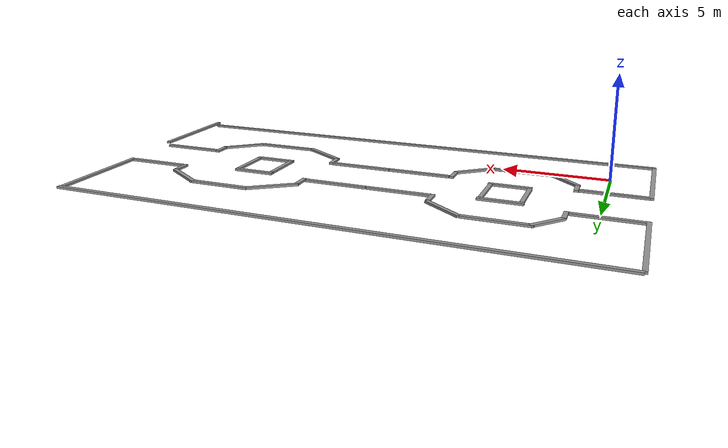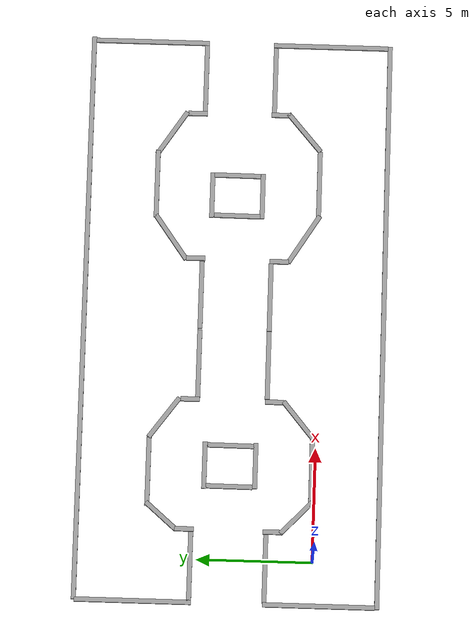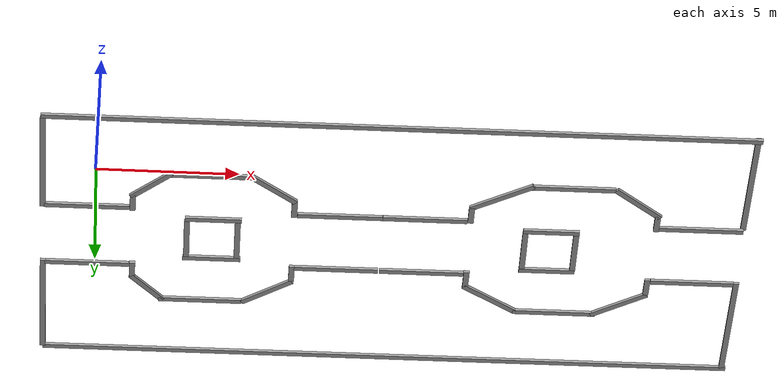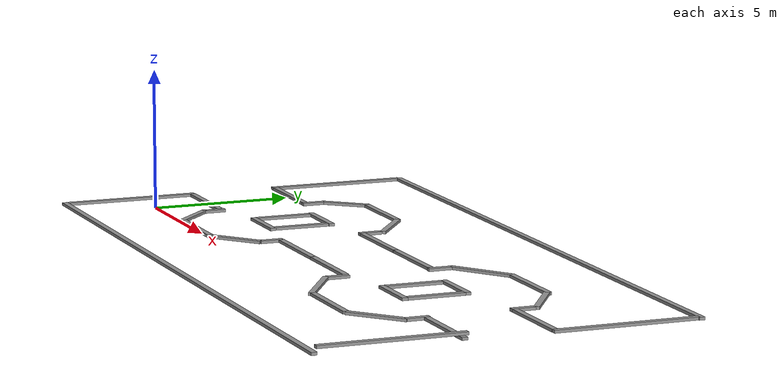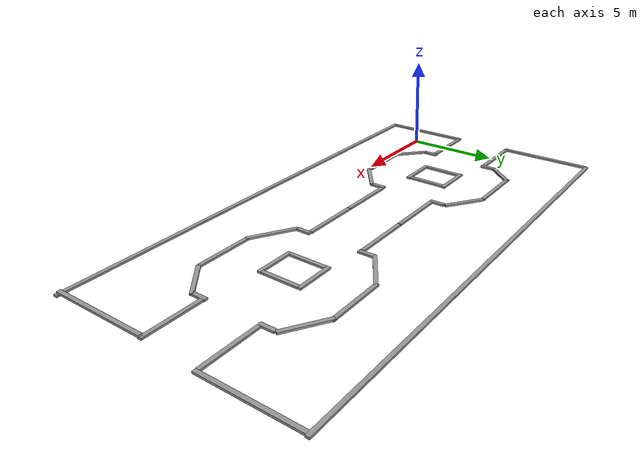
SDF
<?xml version='1.0'?>
<sdf version='1.6'>
  <model name='brick_box_3x1x3'>
    <link name='link_1'>
      <pose frame=''>-1.85709 -0.304134 0.5 0 -0 0</pose>
      <inertial>
        <mass>0.964444</mass>
        <inertia>
          <ixx>0.155127</ixx>
          <ixy>0</ixy>
          <ixz>0</ixz>
          <iyy>0.160741</iyy>
          <iyz>0</iyz>
          <izz>0.155127</izz>
        </inertia>
        <pose frame=''>0 0 0 0 -0 0</pose>
      </inertial>
      <gravity>1</gravity>
      <self_collide>0</self_collide>
      <kinematic>0</kinematic>
      <visual name='visual'>
        <pose frame=''>0 0 -0.5 0 -0 0</pose>
        <geometry>
          <box>
            <size>0.2 4.82222 0.1</size>
          </box>
        </geometry>
        <material>
          <lighting>1</lighting>
          <script>
            <uri>file://media/materials/scripts/gazebo.material</uri>
            <name>Gazebo/Grey</name>
          </script>
          <ambient>0.3 0.3 0.3 1</ambient>
          <diffuse>0.7 0.7 0.7 1</diffuse>
          <specular>0.01 0.01 0.01 1</specular>
          <emissive>0 0 0 1</emissive>
          <shader type='vertex'>
            <normal_map>__default__</normal_map>
          </shader>
        </material>
        <cast_shadows>1</cast_shadows>
        <transparency>0</transparency>
      </visual>
      <collision name='collision'>
        <laser_retro>0</laser_retro>
        <max_contacts>10</max_contacts>
        <pose frame=''>0 0 -0.5 0 -0 0</pose>
        <geometry>
          <box>
            <size>0.1 4.82222 0.2</size>
          </box>
        </geometry>
        <surface>
          <friction>
            <ode>
              <mu>1</mu>
              <mu2>1</mu2>
              <fdir1>0 0 0</fdir1>
              <slip1>0</slip1>
              <slip2>0</slip2>
            </ode>
            <torsional>
              <coefficient>1</coefficient>
              <patch_radius>0</patch_radius>
              <surface_radius>0</surface_radius>
              <use_patch_radius>1</use_patch_radius>
              <ode>
                <slip>0</slip>
              </ode>
            </torsional>
          </friction>
          <bounce>
            <restitution_coefficient>0</restitution_coefficient>
            <threshold>1e+06</threshold>
          </bounce>
          <contact>
            <collide_without_contact>0</collide_without_contact>
            <collide_without_contact_bitmask>1</collide_without_contact_bitmask>
            <collide_bitmask>1</collide_bitmask>
            <ode>
              <soft_cfm>0</soft_cfm>
              <soft_erp>0.2</soft_erp>
              <kp>1e+13</kp>
              <kd>1</kd>
              <max_vel>0.01</max_vel>
              <min_depth>0</min_depth>
            </ode>
            <bullet>
              <split_impulse>1</split_impulse>
              <split_impulse_penetration_threshold>-0.01</split_impulse_penetration_threshold>
              <soft_cfm>0</soft_cfm>
              <soft_erp>0.2</soft_erp>
              <kp>1e+13</kp>
              <kd>1</kd>
            </bullet>
          </contact>
        </surface>
      </collision>
    </link>
    <link name='link_1_clone'>
      <pose frame=''>-1.84895 7.65508 0.5 0 -0 0</pose>
      <inertial>
        <mass>1</mass>
        <inertia>
          <ixx>0.166667</ixx>
          <ixy>0</ixy>
          <ixz>0</ixz>
          <iyy>0.166667</iyy>
          <iyz>0</iyz>
          <izz>0.166667</izz>
        </inertia>
        <pose frame=''>0 0 0 0 -0 0</pose>
      </inertial>
      <self_collide>0</self_collide>
      <kinematic>0</kinematic>
      <visual name='visual'>
        <pose frame=''>0 0 -0.5 0 -0 0</pose>
        <geometry>
          <box>
            <size>0.2 5 0.1</size>
          </box>
        </geometry>
        <material>
          <lighting>1</lighting>
          <script>
            <uri>file://media/materials/scripts/gazebo.material</uri>
            <name>Gazebo/Grey</name>
          </script>
          <ambient>0.3 0.3 0.3 1</ambient>
          <diffuse>0.7 0.7 0.7 1</diffuse>
          <specular>0.01 0.01 0.01 1</specular>
          <emissive>0 0 0 1</emissive>
          <shader type='vertex'>
            <normal_map>__default__</normal_map>
          </shader>
        </material>
        <cast_shadows>1</cast_shadows>
        <transparency>0</transparency>
      </visual>
      <collision name='collision'>
        <laser_retro>0</laser_retro>
        <max_contacts>10</max_contacts>
        <pose frame=''>0 0 -0.5 0 -0 0</pose>
        <geometry>
          <box>
            <size>0.1 5 0.2</size>
          </box>
        </geometry>
        <surface>
          <friction>
            <ode>
              <mu>1</mu>
              <mu2>1</mu2>
              <fdir1>0 0 0</fdir1>
              <slip1>0</slip1>
              <slip2>0</slip2>
            </ode>
            <torsional>
              <coefficient>1</coefficient>
              <patch_radius>0</patch_radius>
              <surface_radius>0</surface_radius>
              <use_patch_radius>1</use_patch_radius>
              <ode>
                <slip>0</slip>
              </ode>
            </torsional>
          </friction>
          <bounce>
            <restitution_coefficient>0</restitution_coefficient>
            <threshold>1e+06</threshold>
          </bounce>
          <contact>
            <collide_without_contact>0</collide_without_contact>
            <collide_without_contact_bitmask>1</collide_without_contact_bitmask>
            <collide_bitmask>1</collide_bitmask>
            <ode>
              <soft_cfm>0</soft_cfm>
              <soft_erp>0.2</soft_erp>
              <kp>1e+13</kp>
              <kd>1</kd>
              <max_vel>0.01</max_vel>
              <min_depth>0</min_depth>
            </ode>
            <bullet>
              <split_impulse>1</split_impulse>
              <split_impulse_penetration_threshold>-0.01</split_impulse_penetration_threshold>
              <soft_cfm>0</soft_cfm>
              <soft_erp>0.2</soft_erp>
              <kp>1e+13</kp>
              <kd>1</kd>
            </bullet>
          </contact>
        </surface>
      </collision>
    </link>
    <link name='link_1_clone_0'>
      <pose frame=''>10.5728 -2.79376 0.5 0 -0 0</pose>
      <inertial>
        <mass>1</mass>
        <inertia>
          <ixx>0.166667</ixx>
          <ixy>0</ixy>
          <ixz>0</ixz>
          <iyy>0.166667</iyy>
          <iyz>0</iyz>
          <izz>0.166667</izz>
        </inertia>
        <pose frame=''>0 0 0 0 -0 0</pose>
      </inertial>
      <self_collide>0</self_collide>
      <kinematic>0</kinematic>
      <gravity>1</gravity>
      <visual name='visual'>
        <pose frame=''>0 0 -0.5 0 -0 0</pose>
        <geometry>
          <box>
            <size>25 0.2 0.1</size>
          </box>
        </geometry>
        <material>
          <lighting>1</lighting>
          <script>
            <uri>file://media/materials/scripts/gazebo.material</uri>
            <name>Gazebo/Grey</name>
          </script>
          <ambient>0.3 0.3 0.3 1</ambient>
          <diffuse>0.7 0.7 0.7 1</diffuse>
          <specular>0.01 0.01 0.01 1</specular>
          <emissive>0 0 0 1</emissive>
          <shader type='vertex'>
            <normal_map>__default__</normal_map>
          </shader>
        </material>
        <cast_shadows>1</cast_shadows>
        <transparency>0</transparency>
      </visual>
      <collision name='collision'>
        <laser_retro>0</laser_retro>
        <max_contacts>10</max_contacts>
        <pose frame=''>0 0 -0.5 0 -0 0</pose>
        <geometry>
          <box>
            <size>25 0.2 0.2</size>
          </box>
        </geometry>
        <surface>
          <friction>
            <ode>
              <mu>1</mu>
              <mu2>1</mu2>
              <fdir1>0 0 0</fdir1>
              <slip1>0</slip1>
              <slip2>0</slip2>
            </ode>
            <torsional>
              <coefficient>1</coefficient>
              <patch_radius>0</patch_radius>
              <surface_radius>0</surface_radius>
              <use_patch_radius>1</use_patch_radius>
              <ode>
                <slip>0</slip>
              </ode>
            </torsional>
          </friction>
          <bounce>
            <restitution_coefficient>0</restitution_coefficient>
            <threshold>1e+06</threshold>
          </bounce>
          <contact>
            <collide_without_contact>0</collide_without_contact>
            <collide_without_contact_bitmask>1</collide_without_contact_bitmask>
            <collide_bitmask>1</collide_bitmask>
            <ode>
              <soft_cfm>0</soft_cfm>
              <soft_erp>0.2</soft_erp>
              <kp>1e+13</kp>
              <kd>1</kd>
              <max_vel>0.01</max_vel>
              <min_depth>0</min_depth>
            </ode>
            <bullet>
              <split_impulse>1</split_impulse>
              <split_impulse_penetration_threshold>-0.01</split_impulse_penetration_threshold>
              <soft_cfm>0</soft_cfm>
              <soft_erp>0.2</soft_erp>
              <kp>1e+13</kp>
              <kd>1</kd>
            </bullet>
          </contact>
        </surface>
      </collision>
    </link>
    <link name='link_1_clone_0_clone'>
      <pose frame=''>10.6572 10.185 0.5 0 -0 0</pose>
      <inertial>
        <mass>1</mass>
        <inertia>
          <ixx>0.166667</ixx>
          <ixy>0</ixy>
          <ixz>0</ixz>
          <iyy>0.166667</iyy>
          <iyz>0</iyz>
          <izz>0.166667</izz>
        </inertia>
        <pose frame=''>0 0 0 0 -0 0</pose>
      </inertial>
      <self_collide>0</self_collide>
      <kinematic>0</kinematic>
      <visual name='visual'>
        <pose frame=''>0 0 -0.5 0 -0 0</pose>
        <geometry>
          <box>
            <size>25 0.2 0.1</size>
          </box>
        </geometry>
        <material>
          <lighting>1</lighting>
          <script>
            <uri>file://media/materials/scripts/gazebo.material</uri>
            <name>Gazebo/Grey</name>
          </script>
          <ambient>0.3 0.3 0.3 1</ambient>
          <diffuse>0.7 0.7 0.7 1</diffuse>
          <specular>0.01 0.01 0.01 1</specular>
          <emissive>0 0 0 1</emissive>
          <shader type='vertex'>
            <normal_map>__default__</normal_map>
          </shader>
        </material>
        <cast_shadows>1</cast_shadows>
        <transparency>0</transparency>
      </visual>
      <collision name='collision'>
        <laser_retro>0</laser_retro>
        <max_contacts>10</max_contacts>
        <pose frame=''>0 0 -0.5 0 -0 0</pose>
        <geometry>
          <box>
            <size>25 0.2 0.2</size>
          </box>
        </geometry>
        <surface>
          <friction>
            <ode>
              <mu>1</mu>
              <mu2>1</mu2>
              <fdir1>0 0 0</fdir1>
              <slip1>0</slip1>
              <slip2>0</slip2>
            </ode>
            <torsional>
              <coefficient>1</coefficient>
              <patch_radius>0</patch_radius>
              <surface_radius>0</surface_radius>
              <use_patch_radius>1</use_patch_radius>
              <ode>
                <slip>0</slip>
              </ode>
            </torsional>
          </friction>
          <bounce>
            <restitution_coefficient>0</restitution_coefficient>
            <threshold>1e+06</threshold>
          </bounce>
          <contact>
            <collide_without_contact>0</collide_without_contact>
            <collide_without_contact_bitmask>1</collide_without_contact_bitmask>
            <collide_bitmask>1</collide_bitmask>
            <ode>
              <soft_cfm>0</soft_cfm>
              <soft_erp>0.2</soft_erp>
              <kp>1e+13</kp>
              <kd>1</kd>
              <max_vel>0.01</max_vel>
              <min_depth>0</min_depth>
            </ode>
            <bullet>
              <split_impulse>1</split_impulse>
              <split_impulse_penetration_threshold>-0.01</split_impulse_penetration_threshold>
              <soft_cfm>0</soft_cfm>
              <soft_erp>0.2</soft_erp>
              <kp>1e+13</kp>
              <kd>1</kd>
            </bullet>
          </contact>
        </surface>
      </collision>
    </link>
    <link name='link_1_clone_1'>
      <pose frame=''>22.9433 -0.208958 0.688101 0 -0 0</pose>
      <inertial>
        <mass>1</mass>
        <inertia>
          <ixx>0.166667</ixx>
          <ixy>0</ixy>
          <ixz>0</ixz>
          <iyy>0.166667</iyy>
          <iyz>0</iyz>
          <izz>0.166667</izz>
        </inertia>
        <pose frame=''>0 0 0 0 -0 0</pose>
      </inertial>
      <self_collide>0</self_collide>
      <kinematic>0</kinematic>
      <visual name='visual'>
        <pose frame=''>0 0 -0.5 0 -0 0</pose>
        <geometry>
          <box>
            <size>0.2 5 0.1</size>
          </box>
        </geometry>
        <material>
          <lighting>1</lighting>
          <script>
            <uri>file://media/materials/scripts/gazebo.material</uri>
            <name>Gazebo/Grey</name>
          </script>
          <ambient>0.3 0.3 0.3 1</ambient>
          <diffuse>0.7 0.7 0.7 1</diffuse>
          <specular>0.01 0.01 0.01 1</specular>
          <emissive>0 0 0 1</emissive>
          <shader type='vertex'>
            <normal_map>__default__</normal_map>
          </shader>
        </material>
        <cast_shadows>1</cast_shadows>
        <transparency>0</transparency>
      </visual>
      <collision name='collision'>
        <laser_retro>0</laser_retro>
        <max_contacts>10</max_contacts>
        <pose frame=''>0 0 -0.5 0 -0 0</pose>
        <geometry>
          <box>
            <size>0.1 5 0.2</size>
          </box>
        </geometry>
        <surface>
          <friction>
            <ode>
              <mu>1</mu>
              <mu2>1</mu2>
              <fdir1>0 0 0</fdir1>
              <slip1>0</slip1>
              <slip2>0</slip2>
            </ode>
            <torsional>
              <coefficient>1</coefficient>
              <patch_radius>0</patch_radius>
              <surface_radius>0</surface_radius>
              <use_patch_radius>1</use_patch_radius>
              <ode>
                <slip>0</slip>
              </ode>
            </torsional>
          </friction>
          <bounce>
            <restitution_coefficient>0</restitution_coefficient>
            <threshold>1e+06</threshold>
          </bounce>
          <contact>
            <collide_without_contact>0</collide_without_contact>
            <collide_without_contact_bitmask>1</collide_without_contact_bitmask>
            <collide_bitmask>1</collide_bitmask>
            <ode>
              <soft_cfm>0</soft_cfm>
              <soft_erp>0.2</soft_erp>
              <kp>1e+13</kp>
              <kd>1</kd>
              <max_vel>0.01</max_vel>
              <min_depth>0</min_depth>
            </ode>
            <bullet>
              <split_impulse>1</split_impulse>
              <split_impulse_penetration_threshold>-0.01</split_impulse_penetration_threshold>
              <soft_cfm>0</soft_cfm>
              <soft_erp>0.2</soft_erp>
              <kp>1e+13</kp>
              <kd>1</kd>
            </bullet>
          </contact>
        </surface>
      </collision>
    </link>
    <link name='link_1_clone_2'>
      <pose frame=''>23.0117 7.63499 0.5 0 -0 0</pose>
      <inertial>
        <mass>1</mass>
        <inertia>
          <ixx>0.166667</ixx>
          <ixy>0</ixy>
          <ixz>0</ixz>
          <iyy>0.166667</iyy>
          <iyz>0</iyz>
          <izz>0.166667</izz>
        </inertia>
        <pose frame=''>0 0 0 0 -0 0</pose>
      </inertial>
      <self_collide>0</self_collide>
      <kinematic>0</kinematic>
      <visual name='visual'>
        <pose frame=''>0 0 -0.5 0 -0 0</pose>
        <geometry>
          <box>
            <size>0.2 5 0.1</size>
          </box>
        </geometry>
        <material>
          <lighting>1</lighting>
          <script>
            <uri>file://media/materials/scripts/gazebo.material</uri>
            <name>Gazebo/Grey</name>
          </script>
          <ambient>0.3 0.3 0.3 1</ambient>
          <diffuse>0.7 0.7 0.7 1</diffuse>
          <specular>0.01 0.01 0.01 1</specular>
          <emissive>0 0 0 1</emissive>
          <shader type='vertex'>
            <normal_map>__default__</normal_map>
          </shader>
        </material>
        <cast_shadows>1</cast_shadows>
        <transparency>0</transparency>
      </visual>
      <collision name='collision'>
        <laser_retro>0</laser_retro>
        <max_contacts>10</max_contacts>
        <pose frame=''>0 0 -0.5 0 -0 0</pose>
        <geometry>
          <box>
            <size>0.1 5 0.2</size>
          </box>
        </geometry>
        <surface>
          <friction>
            <ode>
              <mu>1</mu>
              <mu2>1</mu2>
              <fdir1>0 0 0</fdir1>
              <slip1>0</slip1>
              <slip2>0</slip2>
            </ode>
            <torsional>
              <coefficient>1</coefficient>
              <patch_radius>0</patch_radius>
              <surface_radius>0</surface_radius>
              <use_patch_radius>1</use_patch_radius>
              <ode>
                <slip>0</slip>
              </ode>
            </torsional>
          </friction>
          <bounce>
            <restitution_coefficient>0</restitution_coefficient>
            <threshold>1e+06</threshold>
          </bounce>
          <contact>
            <collide_without_contact>0</collide_without_contact>
            <collide_without_contact_bitmask>1</collide_without_contact_bitmask>
            <collide_bitmask>1</collide_bitmask>
            <ode>
              <soft_cfm>0</soft_cfm>
              <soft_erp>0.2</soft_erp>
              <kp>1e+13</kp>
              <kd>1</kd>
              <max_vel>0.01</max_vel>
              <min_depth>0</min_depth>
            </ode>
            <bullet>
              <split_impulse>1</split_impulse>
              <split_impulse_penetration_threshold>-0.01</split_impulse_penetration_threshold>
              <soft_cfm>0</soft_cfm>
              <soft_erp>0.2</soft_erp>
              <kp>1e+13</kp>
              <kd>1</kd>
            </bullet>
          </contact>
        </surface>
      </collision>
    </link>
    <link name='link_1_clone_3'>
      <pose frame=''>-0.307076 2.03145 0.5 0 -0 0</pose>
      <inertial>
        <mass>1</mass>
        <inertia>
          <ixx>0.166667</ixx>
          <ixy>0</ixy>
          <ixz>0</ixz>
          <iyy>0.166667</iyy>
          <iyz>0</iyz>
          <izz>0.166667</izz>
        </inertia>
        <pose frame=''>0 0 0 0 -0 0</pose>
      </inertial>
      <self_collide>0</self_collide>
      <kinematic>0</kinematic>
      <gravity>1</gravity>
      <visual name='visual'>
        <pose frame=''>0 0 -0.5 0 -0 0</pose>
        <geometry>
          <box>
            <size>3 0.2 0.1</size>
          </box>
        </geometry>
        <material>
          <lighting>1</lighting>
          <script>
            <uri>file://media/materials/scripts/gazebo.material</uri>
            <name>Gazebo/Grey</name>
          </script>
          <ambient>0.3 0.3 0.3 1</ambient>
          <diffuse>0.7 0.7 0.7 1</diffuse>
          <specular>0.01 0.01 0.01 1</specular>
          <emissive>0 0 0 1</emissive>
          <shader type='vertex'>
            <normal_map>__default__</normal_map>
          </shader>
        </material>
        <cast_shadows>1</cast_shadows>
        <transparency>0</transparency>
      </visual>
      <collision name='collision'>
        <laser_retro>0</laser_retro>
        <max_contacts>10</max_contacts>
        <pose frame=''>0 0 -0.5 0 -0 0</pose>
        <geometry>
          <box>
            <size>3 0.2 0.2</size>
          </box>
        </geometry>
        <surface>
          <friction>
            <ode>
              <mu>1</mu>
              <mu2>1</mu2>
              <fdir1>0 0 0</fdir1>
              <slip1>0</slip1>
              <slip2>0</slip2>
            </ode>
            <torsional>
              <coefficient>1</coefficient>
              <patch_radius>0</patch_radius>
              <surface_radius>0</surface_radius>
              <use_patch_radius>1</use_patch_radius>
              <ode>
                <slip>0</slip>
              </ode>
            </torsional>
          </friction>
          <bounce>
            <restitution_coefficient>0</restitution_coefficient>
            <threshold>1e+06</threshold>
          </bounce>
          <contact>
            <collide_without_contact>0</collide_without_contact>
            <collide_without_contact_bitmask>1</collide_without_contact_bitmask>
            <collide_bitmask>1</collide_bitmask>
            <ode>
              <soft_cfm>0</soft_cfm>
              <soft_erp>0.2</soft_erp>
              <kp>1e+13</kp>
              <kd>1</kd>
              <max_vel>0.01</max_vel>
              <min_depth>0</min_depth>
            </ode>
            <bullet>
              <split_impulse>1</split_impulse>
              <split_impulse_penetration_threshold>-0.01</split_impulse_penetration_threshold>
              <soft_cfm>0</soft_cfm>
              <soft_erp>0.2</soft_erp>
              <kp>1e+13</kp>
              <kd>1</kd>
            </bullet>
          </contact>
        </surface>
      </collision>
    </link>
    <link name='link_1_clone_3_clone'>
      <pose frame=''>-0.278142 5.2552 0.5 0 -0 0</pose>
      <inertial>
        <mass>1</mass>
        <inertia>
          <ixx>0.166667</ixx>
          <ixy>0</ixy>
          <ixz>0</ixz>
          <iyy>0.166667</iyy>
          <iyz>0</iyz>
          <izz>0.166667</izz>
        </inertia>
        <pose frame=''>0 0 0 0 -0 0</pose>
      </inertial>
      <self_collide>0</self_collide>
      <kinematic>0</kinematic>
      <visual name='visual'>
        <pose frame=''>0 0 -0.5 0 -0 0</pose>
        <geometry>
          <box>
            <size>3 0.2 0.1</size>
          </box>
        </geometry>
        <material>
          <lighting>1</lighting>
          <script>
            <uri>file://media/materials/scripts/gazebo.material</uri>
            <name>Gazebo/Grey</name>
          </script>
          <ambient>0.3 0.3 0.3 1</ambient>
          <diffuse>0.7 0.7 0.7 1</diffuse>
          <specular>0.01 0.01 0.01 1</specular>
          <emissive>0 0 0 1</emissive>
          <shader type='vertex'>
            <normal_map>__default__</normal_map>
          </shader>
        </material>
        <cast_shadows>1</cast_shadows>
        <transparency>0</transparency>
      </visual>
      <collision name='collision'>
        <laser_retro>0</laser_retro>
        <max_contacts>10</max_contacts>
        <pose frame=''>0 0 -0.5 0 -0 0</pose>
        <geometry>
          <box>
            <size>3 0.2 0.2</size>
          </box>
        </geometry>
        <surface>
          <friction>
            <ode>
              <mu>1</mu>
              <mu2>1</mu2>
              <fdir1>0 0 0</fdir1>
              <slip1>0</slip1>
              <slip2>0</slip2>
            </ode>
            <torsional>
              <coefficient>1</coefficient>
              <patch_radius>0</patch_radius>
              <surface_radius>0</surface_radius>
              <use_patch_radius>1</use_patch_radius>
              <ode>
                <slip>0</slip>
              </ode>
            </torsional>
          </friction>
          <bounce>
            <restitution_coefficient>0</restitution_coefficient>
            <threshold>1e+06</threshold>
          </bounce>
          <contact>
            <collide_without_contact>0</collide_without_contact>
            <collide_without_contact_bitmask>1</collide_without_contact_bitmask>
            <collide_bitmask>1</collide_bitmask>
            <ode>
              <soft_cfm>0</soft_cfm>
              <soft_erp>0.2</soft_erp>
              <kp>1e+13</kp>
              <kd>1</kd>
              <max_vel>0.01</max_vel>
              <min_depth>0</min_depth>
            </ode>
            <bullet>
              <split_impulse>1</split_impulse>
              <split_impulse_penetration_threshold>-0.01</split_impulse_penetration_threshold>
              <soft_cfm>0</soft_cfm>
              <soft_erp>0.2</soft_erp>
              <kp>1e+13</kp>
              <kd>1</kd>
            </bullet>
          </contact>
        </surface>
      </collision>
    </link>
    <link name='link_1_clone_3_clone_0'>
      <pose frame=''>21.4333 2.1957 0.5 0 -0 0</pose>
      <inertial>
        <mass>1</mass>
        <inertia>
          <ixx>0.166667</ixx>
          <ixy>0</ixy>
          <ixz>0</ixz>
          <iyy>0.166667</iyy>
          <iyz>0</iyz>
          <izz>0.166667</izz>
        </inertia>
        <pose frame=''>0 0 0 0 -0 0</pose>
      </inertial>
      <self_collide>0</self_collide>
      <kinematic>0</kinematic>
      <visual name='visual'>
        <pose frame=''>0 0 -0.5 0 -0 0</pose>
        <geometry>
          <box>
            <size>3 0.2 0.1</size>
          </box>
        </geometry>
        <material>
          <lighting>1</lighting>
          <script>
            <uri>file://media/materials/scripts/gazebo.material</uri>
            <name>Gazebo/Grey</name>
          </script>
          <ambient>0.3 0.3 0.3 1</ambient>
          <diffuse>0.7 0.7 0.7 1</diffuse>
          <specular>0.01 0.01 0.01 1</specular>
          <emissive>0 0 0 1</emissive>
          <shader type='vertex'>
            <normal_map>__default__</normal_map>
          </shader>
        </material>
        <cast_shadows>1</cast_shadows>
        <transparency>0</transparency>
      </visual>
      <collision name='collision'>
        <laser_retro>0</laser_retro>
        <max_contacts>10</max_contacts>
        <pose frame=''>0 0 -0.5 0 -0 0</pose>
        <geometry>
          <box>
            <size>3 0.2 0.2</size>
          </box>
        </geometry>
        <surface>
          <friction>
            <ode>
              <mu>1</mu>
              <mu2>1</mu2>
              <fdir1>0 0 0</fdir1>
              <slip1>0</slip1>
              <slip2>0</slip2>
            </ode>
            <torsional>
              <coefficient>1</coefficient>
              <patch_radius>0</patch_radius>
              <surface_radius>0</surface_radius>
              <use_patch_radius>1</use_patch_radius>
              <ode>
                <slip>0</slip>
              </ode>
            </torsional>
          </friction>
          <bounce>
            <restitution_coefficient>0</restitution_coefficient>
            <threshold>1e+06</threshold>
          </bounce>
          <contact>
            <collide_without_contact>0</collide_without_contact>
            <collide_without_contact_bitmask>1</collide_without_contact_bitmask>
            <collide_bitmask>1</collide_bitmask>
            <ode>
              <soft_cfm>0</soft_cfm>
              <soft_erp>0.2</soft_erp>
              <kp>1e+13</kp>
              <kd>1</kd>
              <max_vel>0.01</max_vel>
              <min_depth>0</min_depth>
            </ode>
            <bullet>
              <split_impulse>1</split_impulse>
              <split_impulse_penetration_threshold>-0.01</split_impulse_penetration_threshold>
              <soft_cfm>0</soft_cfm>
              <soft_erp>0.2</soft_erp>
              <kp>1e+13</kp>
              <kd>1</kd>
            </bullet>
          </contact>
        </surface>
      </collision>
    </link>
    <link name='link_1_clone_3_clone_1'>
      <pose frame=''>21.421 5.22151 0.5 0 -0 0</pose>
      <inertial>
        <mass>1</mass>
        <inertia>
          <ixx>0.166667</ixx>
          <ixy>0</ixy>
          <ixz>0</ixz>
          <iyy>0.166667</iyy>
          <iyz>0</iyz>
          <izz>0.166667</izz>
        </inertia>
        <pose frame=''>0 0 0 0 -0 0</pose>
      </inertial>
      <self_collide>0</self_collide>
      <kinematic>0</kinematic>
      <visual name='visual'>
        <pose frame=''>0 0 -0.5 0 -0 0</pose>
        <geometry>
          <box>
            <size>3 0.2 0.1</size>
          </box>
        </geometry>
        <material>
          <lighting>1</lighting>
          <script>
            <uri>file://media/materials/scripts/gazebo.material</uri>
            <name>Gazebo/Grey</name>
          </script>
          <ambient>0.3 0.3 0.3 1</ambient>
          <diffuse>0.7 0.7 0.7 1</diffuse>
          <specular>0.01 0.01 0.01 1</specular>
          <emissive>0 0 0 1</emissive>
          <shader type='vertex'>
            <normal_map>__default__</normal_map>
          </shader>
        </material>
        <cast_shadows>1</cast_shadows>
        <transparency>0</transparency>
      </visual>
      <collision name='collision'>
        <laser_retro>0</laser_retro>
        <max_contacts>10</max_contacts>
        <pose frame=''>0 0 -0.5 0 -0 0</pose>
        <geometry>
          <box>
            <size>3 0.2 0.2</size>
          </box>
        </geometry>
        <surface>
          <friction>
            <ode>
              <mu>1</mu>
              <mu2>1</mu2>
              <fdir1>0 0 0</fdir1>
              <slip1>0</slip1>
              <slip2>0</slip2>
            </ode>
            <torsional>
              <coefficient>1</coefficient>
              <patch_radius>0</patch_radius>
              <surface_radius>0</surface_radius>
              <use_patch_radius>1</use_patch_radius>
              <ode>
                <slip>0</slip>
              </ode>
            </torsional>
          </friction>
          <bounce>
            <restitution_coefficient>0</restitution_coefficient>
            <threshold>1e+06</threshold>
          </bounce>
          <contact>
            <collide_without_contact>0</collide_without_contact>
            <collide_without_contact_bitmask>1</collide_without_contact_bitmask>
            <collide_bitmask>1</collide_bitmask>
            <ode>
              <soft_cfm>0</soft_cfm>
              <soft_erp>0.2</soft_erp>
              <kp>1e+13</kp>
              <kd>1</kd>
              <max_vel>0.01</max_vel>
              <min_depth>0</min_depth>
            </ode>
            <bullet>
              <split_impulse>1</split_impulse>
              <split_impulse_penetration_threshold>-0.01</split_impulse_penetration_threshold>
              <soft_cfm>0</soft_cfm>
              <soft_erp>0.2</soft_erp>
              <kp>1e+13</kp>
              <kd>1</kd>
            </bullet>
          </contact>
        </surface>
      </collision>
    </link>
    <link name='link_1_clone_3_clone_10'>
      <pose frame=''>6.19258 6.57027 0.5 0 0 -0.628314</pose>
      <inertial>
        <mass>0.633292</mass>
        <inertia>
          <ixx>0.107431</ixx>
          <ixy>0</ixy>
          <ixz>0</ixz>
          <iyy>0.0732112</iyy>
          <iyz>0</iyz>
          <izz>0.0750937</izz>
        </inertia>
        <pose frame=''>0 0 0 0 -0 0</pose>
      </inertial>
      <self_collide>0</self_collide>
      <kinematic>0</kinematic>
      <gravity>1</gravity>
      <visual name='visual'>
        <pose frame=''>0 0 -0.5 0 -0 0</pose>
        <geometry>
          <box>
            <size>2.17802 0.203535 0.1</size>
          </box>
        </geometry>
        <material>
          <lighting>1</lighting>
          <script>
            <uri>file://media/materials/scripts/gazebo.material</uri>
            <name>Gazebo/Grey</name>
          </script>
          <ambient>0.3 0.3 0.3 1</ambient>
          <diffuse>0.7 0.7 0.7 1</diffuse>
          <specular>0.01 0.01 0.01 1</specular>
          <emissive>0 0 0 1</emissive>
          <shader type='vertex'>
            <normal_map>__default__</normal_map>
          </shader>
        </material>
        <cast_shadows>1</cast_shadows>
        <transparency>0</transparency>
      </visual>
      <collision name='collision'>
        <laser_retro>0</laser_retro>
        <max_contacts>10</max_contacts>
        <pose frame=''>0 0 -0.5 0 -0 0</pose>
        <geometry>
          <box>
            <size>2.17802 0.203535 0.2</size>
          </box>
        </geometry>
        <surface>
          <friction>
            <ode>
              <mu>1</mu>
              <mu2>1</mu2>
              <fdir1>0 0 0</fdir1>
              <slip1>0</slip1>
              <slip2>0</slip2>
            </ode>
            <torsional>
              <coefficient>1</coefficient>
              <patch_radius>0</patch_radius>
              <surface_radius>0</surface_radius>
              <use_patch_radius>1</use_patch_radius>
              <ode>
                <slip>0</slip>
              </ode>
            </torsional>
          </friction>
          <bounce>
            <restitution_coefficient>0</restitution_coefficient>
            <threshold>1e+06</threshold>
          </bounce>
          <contact>
            <collide_without_contact>0</collide_without_contact>
            <collide_without_contact_bitmask>1</collide_without_contact_bitmask>
            <collide_bitmask>1</collide_bitmask>
            <ode>
              <soft_cfm>0</soft_cfm>
              <soft_erp>0.2</soft_erp>
              <kp>1e+13</kp>
              <kd>1</kd>
              <max_vel>0.01</max_vel>
              <min_depth>0</min_depth>
            </ode>
            <bullet>
              <split_impulse>1</split_impulse>
              <split_impulse_penetration_threshold>-0.01</split_impulse_penetration_threshold>
              <soft_cfm>0</soft_cfm>
              <soft_erp>0.2</soft_erp>
              <kp>1e+13</kp>
              <kd>1</kd>
            </bullet>
          </contact>
        </surface>
      </collision>
    </link>
    <link name='link_1_clone_3_clone_10_clone'>
      <pose frame=''>1.95197 0.748415 0.5 0 0 -0.76059</pose>
      <inertial>
        <mass>0.5645</mass>
        <inertia>
          <ixx>0.0957615</ixx>
          <ixy>0</ixy>
          <ixz>0</ixz>
          <iyy>0.0615164</iyy>
          <iyz>0</iyz>
          <izz>0.0631938</izz>
        </inertia>
        <pose frame=''>0 0 0 0 -0 0</pose>
      </inertial>
      <self_collide>0</self_collide>
      <kinematic>0</kinematic>
      <gravity>1</gravity>
      <visual name='visual'>
        <pose frame=''>0 0 -0.5 0 -0 0</pose>
        <geometry>
          <box>
            <size>1.94144 0.203535 0.1</size>
          </box>
        </geometry>
        <material>
          <lighting>1</lighting>
          <script>
            <uri>file://media/materials/scripts/gazebo.material</uri>
            <name>Gazebo/Grey</name>
          </script>
          <ambient>0.3 0.3 0.3 1</ambient>
          <diffuse>0.7 0.7 0.7 1</diffuse>
          <specular>0.01 0.01 0.01 1</specular>
          <emissive>0 0 0 1</emissive>
          <shader type='vertex'>
            <normal_map>__default__</normal_map>
          </shader>
        </material>
        <cast_shadows>1</cast_shadows>
        <transparency>0</transparency>
      </visual>
      <collision name='collision'>
        <laser_retro>0</laser_retro>
        <max_contacts>10</max_contacts>
        <pose frame=''>0 0 -0.5 0 -0 0</pose>
        <geometry>
          <box>
            <size>1.94144 0.203535 0.2</size>
          </box>
        </geometry>
        <surface>
          <friction>
            <ode>
              <mu>1</mu>
              <mu2>1</mu2>
              <fdir1>0 0 0</fdir1>
              <slip1>0</slip1>
              <slip2>0</slip2>
            </ode>
            <torsional>
              <coefficient>1</coefficient>
              <patch_radius>0</patch_radius>
              <surface_radius>0</surface_radius>
              <use_patch_radius>1</use_patch_radius>
              <ode>
                <slip>0</slip>
              </ode>
            </torsional>
          </friction>
          <bounce>
            <restitution_coefficient>0</restitution_coefficient>
            <threshold>1e+06</threshold>
          </bounce>
          <contact>
            <collide_without_contact>0</collide_without_contact>
            <collide_without_contact_bitmask>1</collide_without_contact_bitmask>
            <collide_bitmask>1</collide_bitmask>
            <ode>
              <soft_cfm>0</soft_cfm>
              <soft_erp>0.2</soft_erp>
              <kp>1e+13</kp>
              <kd>1</kd>
              <max_vel>0.01</max_vel>
              <min_depth>0</min_depth>
            </ode>
            <bullet>
              <split_impulse>1</split_impulse>
              <split_impulse_penetration_threshold>-0.01</split_impulse_penetration_threshold>
              <soft_cfm>0</soft_cfm>
              <soft_erp>0.2</soft_erp>
              <kp>1e+13</kp>
              <kd>1</kd>
            </bullet>
          </contact>
        </surface>
      </collision>
    </link>
    <link name='link_1_clone_3_clone_10_clone_0'>
      <pose frame=''>1.88231 6.56558 0.5 0 0 -2.28733</pose>
      <inertial>
        <mass>0.507827</mass>
        <inertia>
          <ixx>0.0861472</ixx>
          <ixy>0</ixy>
          <ixz>0</ixz>
          <iyy>0.0528569</iyy>
          <iyz>0</iyz>
          <izz>0.0543659</izz>
        </inertia>
        <pose frame=''>0 0 0 0 -0 0</pose>
      </inertial>
      <self_collide>0</self_collide>
      <kinematic>0</kinematic>
      <visual name='visual'>
        <pose frame=''>0 0 -0.5 0 -0 0</pose>
        <geometry>
          <box>
            <size>1.74653 0.203535 0.1</size>
          </box>
        </geometry>
        <material>
          <lighting>1</lighting>
          <script>
            <uri>file://media/materials/scripts/gazebo.material</uri>
            <name>Gazebo/Grey</name>
          </script>
          <ambient>0.3 0.3 0.3 1</ambient>
          <diffuse>0.7 0.7 0.7 1</diffuse>
          <specular>0.01 0.01 0.01 1</specular>
          <emissive>0 0 0 1</emissive>
          <shader type='vertex'>
            <normal_map>__default__</normal_map>
          </shader>
        </material>
        <cast_shadows>1</cast_shadows>
        <transparency>0</transparency>
      </visual>
      <collision name='collision'>
        <laser_retro>0</laser_retro>
        <max_contacts>10</max_contacts>
        <pose frame=''>0 0 -0.5 0 -0 0</pose>
        <geometry>
          <box>
            <size>1.74653 0.203535 0.2</size>
          </box>
        </geometry>
        <surface>
          <friction>
            <ode>
              <mu>1</mu>
              <mu2>1</mu2>
              <fdir1>0 0 0</fdir1>
              <slip1>0</slip1>
              <slip2>0</slip2>
            </ode>
            <torsional>
              <coefficient>1</coefficient>
              <patch_radius>0</patch_radius>
              <surface_radius>0</surface_radius>
              <use_patch_radius>1</use_patch_radius>
              <ode>
                <slip>0</slip>
              </ode>
            </torsional>
          </friction>
          <bounce>
            <restitution_coefficient>0</restitution_coefficient>
            <threshold>1e+06</threshold>
          </bounce>
          <contact>
            <collide_without_contact>0</collide_without_contact>
            <collide_without_contact_bitmask>1</collide_without_contact_bitmask>
            <collide_bitmask>1</collide_bitmask>
            <ode>
              <soft_cfm>0</soft_cfm>
              <soft_erp>0.2</soft_erp>
              <kp>1e+13</kp>
              <kd>1</kd>
              <max_vel>0.01</max_vel>
              <min_depth>0</min_depth>
            </ode>
            <bullet>
              <split_impulse>1</split_impulse>
              <split_impulse_penetration_threshold>-0.01</split_impulse_penetration_threshold>
              <soft_cfm>0</soft_cfm>
              <soft_erp>0.2</soft_erp>
              <kp>1e+13</kp>
              <kd>1</kd>
            </bullet>
          </contact>
        </surface>
      </collision>
    </link>
    <link name='link_1_clone_3_clone_10_clone_1'>
      <pose frame=''>1.30623 1.75197 0.5 0 0 -1.56821</pose>
      <inertial>
        <mass>0.239353</mass>
        <inertia>
          <ixx>0.0406036</ixx>
          <ixy>0</ixy>
          <ixz>0</ixz>
          <iyy>0.0210496</iyy>
          <iyz>0</iyz>
          <izz>0.0217608</izz>
        </inertia>
        <pose frame=''>0 0 0 0 -0 0</pose>
      </inertial>
      <self_collide>0</self_collide>
      <kinematic>0</kinematic>
      <visual name='visual'>
        <pose frame=''>0 0 -0.5 0 -0 0</pose>
        <geometry>
          <box>
            <size>0.823187 0.203535 0.1</size>
          </box>
        </geometry>
        <material>
          <lighting>1</lighting>
          <script>
            <uri>file://media/materials/scripts/gazebo.material</uri>
            <name>Gazebo/Grey</name>
          </script>
          <ambient>0.3 0.3 0.3 1</ambient>
          <diffuse>0.7 0.7 0.7 1</diffuse>
          <specular>0.01 0.01 0.01 1</specular>
          <emissive>0 0 0 1</emissive>
          <shader type='vertex'>
            <normal_map>__default__</normal_map>
          </shader>
        </material>
        <cast_shadows>1</cast_shadows>
        <transparency>0</transparency>
      </visual>
      <collision name='collision'>
        <laser_retro>0</laser_retro>
        <max_contacts>10</max_contacts>
        <pose frame=''>0 0 -0.5 0 -0 0</pose>
        <geometry>
          <box>
            <size>0.823187 0.203535 0.2</size>
          </box>
        </geometry>
        <surface>
          <friction>
            <ode>
              <mu>1</mu>
              <mu2>1</mu2>
              <fdir1>0 0 0</fdir1>
              <slip1>0</slip1>
              <slip2>0</slip2>
            </ode>
            <torsional>
              <coefficient>1</coefficient>
              <patch_radius>0</patch_radius>
              <surface_radius>0</surface_radius>
              <use_patch_radius>1</use_patch_radius>
              <ode>
                <slip>0</slip>
              </ode>
            </torsional>
          </friction>
          <bounce>
            <restitution_coefficient>0</restitution_coefficient>
            <threshold>1e+06</threshold>
          </bounce>
          <contact>
            <collide_without_contact>0</collide_without_contact>
            <collide_without_contact_bitmask>1</collide_without_contact_bitmask>
            <collide_bitmask>1</collide_bitmask>
            <ode>
              <soft_cfm>0</soft_cfm>
              <soft_erp>0.2</soft_erp>
              <kp>1e+13</kp>
              <kd>1</kd>
              <max_vel>0.01</max_vel>
              <min_depth>0</min_depth>
            </ode>
            <bullet>
              <split_impulse>1</split_impulse>
              <split_impulse_penetration_threshold>-0.01</split_impulse_penetration_threshold>
              <soft_cfm>0</soft_cfm>
              <soft_erp>0.2</soft_erp>
              <kp>1e+13</kp>
              <kd>1</kd>
            </bullet>
          </contact>
        </surface>
      </collision>
    </link>
    <link name='link_1_clone_3_clone_10_clone_1_clone'>
      <pose frame=''>1.33845 5.54897 0.5 0 0 -1.56821</pose>
      <inertial>
        <mass>0.239353</mass>
        <inertia>
          <ixx>0.0406036</ixx>
          <ixy>0</ixy>
          <ixz>0</ixz>
          <iyy>0.0210496</iyy>
          <iyz>0</iyz>
          <izz>0.0217608</izz>
        </inertia>
        <pose frame=''>0 0 0 0 -0 0</pose>
      </inertial>
      <self_collide>0</self_collide>
      <kinematic>0</kinematic>
      <visual name='visual'>
        <pose frame=''>0 0 -0.5 0 -0 0</pose>
        <geometry>
          <box>
            <size>0.823187 0.203535 0.1</size>
          </box>
        </geometry>
        <material>
          <lighting>1</lighting>
          <script>
            <uri>file://media/materials/scripts/gazebo.material</uri>
            <name>Gazebo/Grey</name>
          </script>
          <ambient>0.3 0.3 0.3 1</ambient>
          <diffuse>0.7 0.7 0.7 1</diffuse>
          <specular>0.01 0.01 0.01 1</specular>
          <emissive>0 0 0 1</emissive>
          <shader type='vertex'>
            <normal_map>__default__</normal_map>
          </shader>
        </material>
        <cast_shadows>1</cast_shadows>
        <transparency>0</transparency>
      </visual>
      <collision name='collision'>
        <laser_retro>0</laser_retro>
        <max_contacts>10</max_contacts>
        <pose frame=''>0 0 -0.5 0 -0 0</pose>
        <geometry>
          <box>
            <size>0.823187 0.203535 0.2</size>
          </box>
        </geometry>
        <surface>
          <friction>
            <ode>
              <mu>1</mu>
              <mu2>1</mu2>
              <fdir1>0 0 0</fdir1>
              <slip1>0</slip1>
              <slip2>0</slip2>
            </ode>
            <torsional>
              <coefficient>1</coefficient>
              <patch_radius>0</patch_radius>
              <surface_radius>0</surface_radius>
              <use_patch_radius>1</use_patch_radius>
              <ode>
                <slip>0</slip>
              </ode>
            </torsional>
          </friction>
          <bounce>
            <restitution_coefficient>0</restitution_coefficient>
            <threshold>1e+06</threshold>
          </bounce>
          <contact>
            <collide_without_contact>0</collide_without_contact>
            <collide_without_contact_bitmask>1</collide_without_contact_bitmask>
            <collide_bitmask>1</collide_bitmask>
            <ode>
              <soft_cfm>0</soft_cfm>
              <soft_erp>0.2</soft_erp>
              <kp>1e+13</kp>
              <kd>1</kd>
              <max_vel>0.01</max_vel>
              <min_depth>0</min_depth>
            </ode>
            <bullet>
              <split_impulse>1</split_impulse>
              <split_impulse_penetration_threshold>-0.01</split_impulse_penetration_threshold>
              <soft_cfm>0</soft_cfm>
              <soft_erp>0.2</soft_erp>
              <kp>1e+13</kp>
              <kd>1</kd>
            </bullet>
          </contact>
        </surface>
      </collision>
    </link>
    <link name='link_1_clone_3_clone_10_clone_1_clone_0'>
      <pose frame=''>7.00342 1.81838 0.5 0 0 -1.56821</pose>
      <inertial>
        <mass>0.239353</mass>
        <inertia>
          <ixx>0.0406036</ixx>
          <ixy>0</ixy>
          <ixz>0</ixz>
          <iyy>0.0210496</iyy>
          <iyz>0</iyz>
          <izz>0.0217608</izz>
        </inertia>
        <pose frame=''>0 0 0 0 -0 0</pose>
      </inertial>
      <self_collide>0</self_collide>
      <kinematic>0</kinematic>
      <visual name='visual'>
        <pose frame=''>0 0 -0.5 0 -0 0</pose>
        <geometry>
          <box>
            <size>0.823187 0.203535 0.1</size>
          </box>
        </geometry>
        <material>
          <lighting>1</lighting>
          <script>
            <uri>file://media/materials/scripts/gazebo.material</uri>
            <name>Gazebo/Grey</name>
          </script>
          <ambient>0.3 0.3 0.3 1</ambient>
          <diffuse>0.7 0.7 0.7 1</diffuse>
          <specular>0.01 0.01 0.01 1</specular>
          <emissive>0 0 0 1</emissive>
          <shader type='vertex'>
            <normal_map>__default__</normal_map>
          </shader>
        </material>
        <cast_shadows>1</cast_shadows>
        <transparency>0</transparency>
      </visual>
      <collision name='collision'>
        <laser_retro>0</laser_retro>
        <max_contacts>10</max_contacts>
        <pose frame=''>0 0 -0.5 0 -0 0</pose>
        <geometry>
          <box>
            <size>0.823187 0.203535 0.2</size>
          </box>
        </geometry>
        <surface>
          <friction>
            <ode>
              <mu>1</mu>
              <mu2>1</mu2>
              <fdir1>0 0 0</fdir1>
              <slip1>0</slip1>
              <slip2>0</slip2>
            </ode>
            <torsional>
              <coefficient>1</coefficient>
              <patch_radius>0</patch_radius>
              <surface_radius>0</surface_radius>
              <use_patch_radius>1</use_patch_radius>
              <ode>
                <slip>0</slip>
              </ode>
            </torsional>
          </friction>
          <bounce>
            <restitution_coefficient>0</restitution_coefficient>
            <threshold>1e+06</threshold>
          </bounce>
          <contact>
            <collide_without_contact>0</collide_without_contact>
            <collide_without_contact_bitmask>1</collide_without_contact_bitmask>
            <collide_bitmask>1</collide_bitmask>
            <ode>
              <soft_cfm>0</soft_cfm>
              <soft_erp>0.2</soft_erp>
              <kp>1e+13</kp>
              <kd>1</kd>
              <max_vel>0.01</max_vel>
              <min_depth>0</min_depth>
            </ode>
            <bullet>
              <split_impulse>1</split_impulse>
              <split_impulse_penetration_threshold>-0.01</split_impulse_penetration_threshold>
              <soft_cfm>0</soft_cfm>
              <soft_erp>0.2</soft_erp>
              <kp>1e+13</kp>
              <kd>1</kd>
            </bullet>
          </contact>
        </surface>
      </collision>
    </link>
    <link name='link_1_clone_3_clone_10_clone_1_clone_1'>
      <pose frame=''>7.04036 5.46158 0.5 0 0 -1.56821</pose>
      <inertial>
        <mass>0.239353</mass>
        <inertia>
          <ixx>0.0406036</ixx>
          <ixy>0</ixy>
          <ixz>0</ixz>
          <iyy>0.0210496</iyy>
          <iyz>0</iyz>
          <izz>0.0217608</izz>
        </inertia>
        <pose frame=''>0 0 0 0 -0 0</pose>
      </inertial>
      <self_collide>0</self_collide>
      <kinematic>0</kinematic>
      <visual name='visual'>
        <pose frame=''>0 0 -0.5 0 -0 0</pose>
        <geometry>
          <box>
            <size>0.823187 0.203535 0.1</size>
          </box>
        </geometry>
        <material>
          <lighting>1</lighting>
          <script>
            <uri>file://media/materials/scripts/gazebo.material</uri>
            <name>Gazebo/Grey</name>
          </script>
          <ambient>0.3 0.3 0.3 1</ambient>
          <diffuse>0.7 0.7 0.7 1</diffuse>
          <specular>0.01 0.01 0.01 1</specular>
          <emissive>0 0 0 1</emissive>
          <shader type='vertex'>
            <normal_map>__default__</normal_map>
          </shader>
        </material>
        <cast_shadows>1</cast_shadows>
        <transparency>0</transparency>
      </visual>
      <collision name='collision'>
        <laser_retro>0</laser_retro>
        <max_contacts>10</max_contacts>
        <pose frame=''>0 0 -0.5 0 -0 0</pose>
        <geometry>
          <box>
            <size>0.823187 0.203535 0.2</size>
          </box>
        </geometry>
        <surface>
          <friction>
            <ode>
              <mu>1</mu>
              <mu2>1</mu2>
              <fdir1>0 0 0</fdir1>
              <slip1>0</slip1>
              <slip2>0</slip2>
            </ode>
            <torsional>
              <coefficient>1</coefficient>
              <patch_radius>0</patch_radius>
              <surface_radius>0</surface_radius>
              <use_patch_radius>1</use_patch_radius>
              <ode>
                <slip>0</slip>
              </ode>
            </torsional>
          </friction>
          <bounce>
            <restitution_coefficient>0</restitution_coefficient>
            <threshold>1e+06</threshold>
          </bounce>
          <contact>
            <collide_without_contact>0</collide_without_contact>
            <collide_without_contact_bitmask>1</collide_without_contact_bitmask>
            <collide_bitmask>1</collide_bitmask>
            <ode>
              <soft_cfm>0</soft_cfm>
              <soft_erp>0.2</soft_erp>
              <kp>1e+13</kp>
              <kd>1</kd>
              <max_vel>0.01</max_vel>
              <min_depth>0</min_depth>
            </ode>
            <bullet>
              <split_impulse>1</split_impulse>
              <split_impulse_penetration_threshold>-0.01</split_impulse_penetration_threshold>
              <soft_cfm>0</soft_cfm>
              <soft_erp>0.2</soft_erp>
              <kp>1e+13</kp>
              <kd>1</kd>
            </bullet>
          </contact>
        </surface>
      </collision>
    </link>
    <link name='link_1_clone_3_clone_10_clone_1_clone_2'>
      <pose frame=''>13.2467 1.79727 0.5 0 0 -1.56821</pose>
      <inertial>
        <mass>0.239353</mass>
        <inertia>
          <ixx>0.0406036</ixx>
          <ixy>0</ixy>
          <ixz>0</ixz>
          <iyy>0.0210496</iyy>
          <iyz>0</iyz>
          <izz>0.0217608</izz>
        </inertia>
        <pose frame=''>0 0 0 0 -0 0</pose>
      </inertial>
      <self_collide>0</self_collide>
      <kinematic>0</kinematic>
      <visual name='visual'>
        <pose frame=''>0 0 -0.5 0 -0 0</pose>
        <geometry>
          <box>
            <size>0.823187 0.203535 0.1</size>
          </box>
        </geometry>
        <material>
          <lighting>1</lighting>
          <script>
            <uri>file://media/materials/scripts/gazebo.material</uri>
            <name>Gazebo/Grey</name>
          </script>
          <ambient>0.3 0.3 0.3 1</ambient>
          <diffuse>0.7 0.7 0.7 1</diffuse>
          <specular>0.01 0.01 0.01 1</specular>
          <emissive>0 0 0 1</emissive>
          <shader type='vertex'>
            <normal_map>__default__</normal_map>
          </shader>
        </material>
        <cast_shadows>1</cast_shadows>
        <transparency>0</transparency>
      </visual>
      <collision name='collision'>
        <laser_retro>0</laser_retro>
        <max_contacts>10</max_contacts>
        <pose frame=''>0 0 -0.5 0 -0 0</pose>
        <geometry>
          <box>
            <size>0.823187 0.203535 0.2</size>
          </box>
        </geometry>
        <surface>
          <friction>
            <ode>
              <mu>1</mu>
              <mu2>1</mu2>
              <fdir1>0 0 0</fdir1>
              <slip1>0</slip1>
              <slip2>0</slip2>
            </ode>
            <torsional>
              <coefficient>1</coefficient>
              <patch_radius>0</patch_radius>
              <surface_radius>0</surface_radius>
              <use_patch_radius>1</use_patch_radius>
              <ode>
                <slip>0</slip>
              </ode>
            </torsional>
          </friction>
          <bounce>
            <restitution_coefficient>0</restitution_coefficient>
            <threshold>1e+06</threshold>
          </bounce>
          <contact>
            <collide_without_contact>0</collide_without_contact>
            <collide_without_contact_bitmask>1</collide_without_contact_bitmask>
            <collide_bitmask>1</collide_bitmask>
            <ode>
              <soft_cfm>0</soft_cfm>
              <soft_erp>0.2</soft_erp>
              <kp>1e+13</kp>
              <kd>1</kd>
              <max_vel>0.01</max_vel>
              <min_depth>0</min_depth>
            </ode>
            <bullet>
              <split_impulse>1</split_impulse>
              <split_impulse_penetration_threshold>-0.01</split_impulse_penetration_threshold>
              <soft_cfm>0</soft_cfm>
              <soft_erp>0.2</soft_erp>
              <kp>1e+13</kp>
              <kd>1</kd>
            </bullet>
          </contact>
        </surface>
      </collision>
    </link>
    <link name='link_1_clone_3_clone_10_clone_1_clone_3'>
      <pose frame=''>13.302 5.42831 0.5 0 0 -1.56821</pose>
      <inertial>
        <mass>0.239353</mass>
        <inertia>
          <ixx>0.0406036</ixx>
          <ixy>0</ixy>
          <ixz>0</ixz>
          <iyy>0.0210496</iyy>
          <iyz>0</iyz>
          <izz>0.0217608</izz>
        </inertia>
        <pose frame=''>0 0 0 0 -0 0</pose>
      </inertial>
      <self_collide>0</self_collide>
      <kinematic>0</kinematic>
      <visual name='visual'>
        <pose frame=''>0 0 -0.5 0 -0 0</pose>
        <geometry>
          <box>
            <size>0.823187 0.203535 0.1</size>
          </box>
        </geometry>
        <material>
          <lighting>1</lighting>
          <script>
            <uri>file://media/materials/scripts/gazebo.material</uri>
            <name>Gazebo/Grey</name>
          </script>
          <ambient>0.3 0.3 0.3 1</ambient>
          <diffuse>0.7 0.7 0.7 1</diffuse>
          <specular>0.01 0.01 0.01 1</specular>
          <emissive>0 0 0 1</emissive>
          <shader type='vertex'>
            <normal_map>__default__</normal_map>
          </shader>
        </material>
        <cast_shadows>1</cast_shadows>
        <transparency>0</transparency>
      </visual>
      <collision name='collision'>
        <laser_retro>0</laser_retro>
        <max_contacts>10</max_contacts>
        <pose frame=''>0 0 -0.5 0 -0 0</pose>
        <geometry>
          <box>
            <size>0.823187 0.203535 0.2</size>
          </box>
        </geometry>
        <surface>
          <friction>
            <ode>
              <mu>1</mu>
              <mu2>1</mu2>
              <fdir1>0 0 0</fdir1>
              <slip1>0</slip1>
              <slip2>0</slip2>
            </ode>
            <torsional>
              <coefficient>1</coefficient>
              <patch_radius>0</patch_radius>
              <surface_radius>0</surface_radius>
              <use_patch_radius>1</use_patch_radius>
              <ode>
                <slip>0</slip>
              </ode>
            </torsional>
          </friction>
          <bounce>
            <restitution_coefficient>0</restitution_coefficient>
            <threshold>1e+06</threshold>
          </bounce>
          <contact>
            <collide_without_contact>0</collide_without_contact>
            <collide_without_contact_bitmask>1</collide_without_contact_bitmask>
            <collide_bitmask>1</collide_bitmask>
            <ode>
              <soft_cfm>0</soft_cfm>
              <soft_erp>0.2</soft_erp>
              <kp>1e+13</kp>
              <kd>1</kd>
              <max_vel>0.01</max_vel>
              <min_depth>0</min_depth>
            </ode>
            <bullet>
              <split_impulse>1</split_impulse>
              <split_impulse_penetration_threshold>-0.01</split_impulse_penetration_threshold>
              <soft_cfm>0</soft_cfm>
              <soft_erp>0.2</soft_erp>
              <kp>1e+13</kp>
              <kd>1</kd>
            </bullet>
          </contact>
        </surface>
      </collision>
    </link>
    <link name='link_1_clone_3_clone_10_clone_1_clone_4'>
      <pose frame=''>19.8376 1.90733 0.5 0 0 -1.56821</pose>
      <inertial>
        <mass>0.239353</mass>
        <inertia>
          <ixx>0.0406036</ixx>
          <ixy>0</ixy>
          <ixz>0</ixz>
          <iyy>0.0210496</iyy>
          <iyz>0</iyz>
          <izz>0.0217608</izz>
        </inertia>
        <pose frame=''>0 0 0 0 -0 0</pose>
      </inertial>
      <self_collide>0</self_collide>
      <kinematic>0</kinematic>
      <visual name='visual'>
        <pose frame=''>0 0 -0.5 0 -0 0</pose>
        <geometry>
          <box>
            <size>0.823187 0.203535 0.1</size>
          </box>
        </geometry>
        <material>
          <lighting>1</lighting>
          <script>
            <uri>file://media/materials/scripts/gazebo.material</uri>
            <name>Gazebo/Grey</name>
          </script>
          <ambient>0.3 0.3 0.3 1</ambient>
          <diffuse>0.7 0.7 0.7 1</diffuse>
          <specular>0.01 0.01 0.01 1</specular>
          <emissive>0 0 0 1</emissive>
          <shader type='vertex'>
            <normal_map>__default__</normal_map>
          </shader>
        </material>
        <cast_shadows>1</cast_shadows>
        <transparency>0</transparency>
      </visual>
      <collision name='collision'>
        <laser_retro>0</laser_retro>
        <max_contacts>10</max_contacts>
        <pose frame=''>0 0 -0.5 0 -0 0</pose>
        <geometry>
          <box>
            <size>0.823187 0.203535 0.2</size>
          </box>
        </geometry>
        <surface>
          <friction>
            <ode>
              <mu>1</mu>
              <mu2>1</mu2>
              <fdir1>0 0 0</fdir1>
              <slip1>0</slip1>
              <slip2>0</slip2>
            </ode>
            <torsional>
              <coefficient>1</coefficient>
              <patch_radius>0</patch_radius>
              <surface_radius>0</surface_radius>
              <use_patch_radius>1</use_patch_radius>
              <ode>
                <slip>0</slip>
              </ode>
            </torsional>
          </friction>
          <bounce>
            <restitution_coefficient>0</restitution_coefficient>
            <threshold>1e+06</threshold>
          </bounce>
          <contact>
            <collide_without_contact>0</collide_without_contact>
            <collide_without_contact_bitmask>1</collide_without_contact_bitmask>
            <collide_bitmask>1</collide_bitmask>
            <ode>
              <soft_cfm>0</soft_cfm>
              <soft_erp>0.2</soft_erp>
              <kp>1e+13</kp>
              <kd>1</kd>
              <max_vel>0.01</max_vel>
              <min_depth>0</min_depth>
            </ode>
            <bullet>
              <split_impulse>1</split_impulse>
              <split_impulse_penetration_threshold>-0.01</split_impulse_penetration_threshold>
              <soft_cfm>0</soft_cfm>
              <soft_erp>0.2</soft_erp>
              <kp>1e+13</kp>
              <kd>1</kd>
            </bullet>
          </contact>
        </surface>
      </collision>
    </link>
    <link name='link_1_clone_3_clone_10_clone_1_clone_5'>
      <pose frame=''>19.8123 5.5335 0.5 0 0 -1.56821</pose>
      <inertial>
        <mass>0.239353</mass>
        <inertia>
          <ixx>0.0406036</ixx>
          <ixy>0</ixy>
          <ixz>0</ixz>
          <iyy>0.0210496</iyy>
          <iyz>0</iyz>
          <izz>0.0217608</izz>
        </inertia>
        <pose frame=''>0 0 0 0 -0 0</pose>
      </inertial>
      <self_collide>0</self_collide>
      <kinematic>0</kinematic>
      <visual name='visual'>
        <pose frame=''>0 0 -0.5 0 -0 0</pose>
        <geometry>
          <box>
            <size>0.823187 0.203535 0.1</size>
          </box>
        </geometry>
        <material>
          <lighting>1</lighting>
          <script>
            <uri>file://media/materials/scripts/gazebo.material</uri>
            <name>Gazebo/Grey</name>
          </script>
          <ambient>0.3 0.3 0.3 1</ambient>
          <diffuse>0.7 0.7 0.7 1</diffuse>
          <specular>0.01 0.01 0.01 1</specular>
          <emissive>0 0 0 1</emissive>
          <shader type='vertex'>
            <normal_map>__default__</normal_map>
          </shader>
        </material>
        <cast_shadows>1</cast_shadows>
        <transparency>0</transparency>
      </visual>
      <collision name='collision'>
        <laser_retro>0</laser_retro>
        <max_contacts>10</max_contacts>
        <pose frame=''>0 0 -0.5 0 -0 0</pose>
        <geometry>
          <box>
            <size>0.823187 0.203535 0.2</size>
          </box>
        </geometry>
        <surface>
          <friction>
            <ode>
              <mu>1</mu>
              <mu2>1</mu2>
              <fdir1>0 0 0</fdir1>
              <slip1>0</slip1>
              <slip2>0</slip2>
            </ode>
            <torsional>
              <coefficient>1</coefficient>
              <patch_radius>0</patch_radius>
              <surface_radius>0</surface_radius>
              <use_patch_radius>1</use_patch_radius>
              <ode>
                <slip>0</slip>
              </ode>
            </torsional>
          </friction>
          <bounce>
            <restitution_coefficient>0</restitution_coefficient>
            <threshold>1e+06</threshold>
          </bounce>
          <contact>
            <collide_without_contact>0</collide_without_contact>
            <collide_without_contact_bitmask>1</collide_without_contact_bitmask>
            <collide_bitmask>1</collide_bitmask>
            <ode>
              <soft_cfm>0</soft_cfm>
              <soft_erp>0.2</soft_erp>
              <kp>1e+13</kp>
              <kd>1</kd>
              <max_vel>0.01</max_vel>
              <min_depth>0</min_depth>
            </ode>
            <bullet>
              <split_impulse>1</split_impulse>
              <split_impulse_penetration_threshold>-0.01</split_impulse_penetration_threshold>
              <soft_cfm>0</soft_cfm>
              <soft_erp>0.2</soft_erp>
              <kp>1e+13</kp>
              <kd>1</kd>
            </bullet>
          </contact>
        </surface>
      </collision>
    </link>
    <link name='link_1_clone_3_clone_10_clone_2'>
      <pose frame=''>6.23458 0.770061 0.5 0 0 -2.45426</pose>
      <inertial>
        <mass>0.603389</mass>
        <inertia>
          <ixx>0.102359</ixx>
          <ixy>0</ixy>
          <ixz>0</ixz>
          <iyy>0.0679589</iyy>
          <iyz>0</iyz>
          <izz>0.0697524</izz>
        </inertia>
        <pose frame=''>0 0 0 0 -0 0</pose>
      </inertial>
      <self_collide>0</self_collide>
      <kinematic>0</kinematic>
      <visual name='visual'>
        <pose frame=''>0 0 -0.5 0 -0 0</pose>
        <geometry>
          <box>
            <size>2.07517 0.203535 0.1</size>
          </box>
        </geometry>
        <material>
          <lighting>1</lighting>
          <script>
            <uri>file://media/materials/scripts/gazebo.material</uri>
            <name>Gazebo/Grey</name>
          </script>
          <ambient>0.3 0.3 0.3 1</ambient>
          <diffuse>0.7 0.7 0.7 1</diffuse>
          <specular>0.01 0.01 0.01 1</specular>
          <emissive>0 0 0 1</emissive>
          <shader type='vertex'>
            <normal_map>__default__</normal_map>
          </shader>
        </material>
        <cast_shadows>1</cast_shadows>
        <transparency>0</transparency>
      </visual>
      <collision name='collision'>
        <laser_retro>0</laser_retro>
        <max_contacts>10</max_contacts>
        <pose frame=''>0 0 -0.5 0 -0 0</pose>
        <geometry>
          <box>
            <size>2.07517 0.203535 0.2</size>
          </box>
        </geometry>
        <surface>
          <friction>
            <ode>
              <mu>1</mu>
              <mu2>1</mu2>
              <fdir1>0 0 0</fdir1>
              <slip1>0</slip1>
              <slip2>0</slip2>
            </ode>
            <torsional>
              <coefficient>1</coefficient>
              <patch_radius>0</patch_radius>
              <surface_radius>0</surface_radius>
              <use_patch_radius>1</use_patch_radius>
              <ode>
                <slip>0</slip>
              </ode>
            </torsional>
          </friction>
          <bounce>
            <restitution_coefficient>0</restitution_coefficient>
            <threshold>1e+06</threshold>
          </bounce>
          <contact>
            <collide_without_contact>0</collide_without_contact>
            <collide_without_contact_bitmask>1</collide_without_contact_bitmask>
            <collide_bitmask>1</collide_bitmask>
            <ode>
              <soft_cfm>0</soft_cfm>
              <soft_erp>0.2</soft_erp>
              <kp>1e+13</kp>
              <kd>1</kd>
              <max_vel>0.01</max_vel>
              <min_depth>0</min_depth>
            </ode>
            <bullet>
              <split_impulse>1</split_impulse>
              <split_impulse_penetration_threshold>-0.01</split_impulse_penetration_threshold>
              <soft_cfm>0</soft_cfm>
              <soft_erp>0.2</soft_erp>
              <kp>1e+13</kp>
              <kd>1</kd>
            </bullet>
          </contact>
        </surface>
      </collision>
    </link>
    <link name='link_1_clone_3_clone_10_clone_4'>
      <pose frame=''>18.8978 6.62107 0.5 0 0 -0.579619</pose>
      <inertial>
        <mass>0.66633</mass>
        <inertia>
          <ixx>0.113036</ixx>
          <ixy>0</ixy>
          <ixz>0</ixz>
          <iyy>0.0793326</iyy>
          <iyz>0</iyz>
          <izz>0.0813132</izz>
        </inertia>
        <pose frame=''>0 0 0 0 -0 0</pose>
      </inertial>
      <self_collide>0</self_collide>
      <kinematic>0</kinematic>
      <visual name='visual'>
        <pose frame=''>0 0 -0.5 0 -0 0</pose>
        <geometry>
          <box>
            <size>2.29164 0.203535 0.1</size>
          </box>
        </geometry>
        <material>
          <lighting>1</lighting>
          <script>
            <uri>file://media/materials/scripts/gazebo.material</uri>
            <name>Gazebo/Grey</name>
          </script>
          <ambient>0.3 0.3 0.3 1</ambient>
          <diffuse>0.7 0.7 0.7 1</diffuse>
          <specular>0.01 0.01 0.01 1</specular>
          <emissive>0 0 0 1</emissive>
          <shader type='vertex'>
            <normal_map>__default__</normal_map>
          </shader>
        </material>
        <cast_shadows>1</cast_shadows>
        <transparency>0</transparency>
      </visual>
      <collision name='collision'>
        <laser_retro>0</laser_retro>
        <max_contacts>10</max_contacts>
        <pose frame=''>0 0 -0.5 0 -0 0</pose>
        <geometry>
          <box>
            <size>2.29164 0.203535 0.2</size>
          </box>
        </geometry>
        <surface>
          <friction>
            <ode>
              <mu>1</mu>
              <mu2>1</mu2>
              <fdir1>0 0 0</fdir1>
              <slip1>0</slip1>
              <slip2>0</slip2>
            </ode>
            <torsional>
              <coefficient>1</coefficient>
              <patch_radius>0</patch_radius>
              <surface_radius>0</surface_radius>
              <use_patch_radius>1</use_patch_radius>
              <ode>
                <slip>0</slip>
              </ode>
            </torsional>
          </friction>
          <bounce>
            <restitution_coefficient>0</restitution_coefficient>
            <threshold>1e+06</threshold>
          </bounce>
          <contact>
            <collide_without_contact>0</collide_without_contact>
            <collide_without_contact_bitmask>1</collide_without_contact_bitmask>
            <collide_bitmask>1</collide_bitmask>
            <ode>
              <soft_cfm>0</soft_cfm>
              <soft_erp>0.2</soft_erp>
              <kp>1e+13</kp>
              <kd>1</kd>
              <max_vel>0.01</max_vel>
              <min_depth>0</min_depth>
            </ode>
            <bullet>
              <split_impulse>1</split_impulse>
              <split_impulse_penetration_threshold>-0.01</split_impulse_penetration_threshold>
              <soft_cfm>0</soft_cfm>
              <soft_erp>0.2</soft_erp>
              <kp>1e+13</kp>
              <kd>1</kd>
            </bullet>
          </contact>
        </surface>
      </collision>
    </link>
    <link name='link_1_clone_3_clone_10_clone_4_clone'>
      <pose frame=''>14.2781 0.747531 0.5 0 0 -0.55659</pose>
      <inertial>
        <mass>0.726749</mass>
        <inertia>
          <ixx>0.123285</ixx>
          <ixy>0</ixy>
          <ixz>0</ixz>
          <iyy>0.0914481</iyy>
          <iyz>0</iyz>
          <izz>0.0936075</izz>
        </inertia>
        <pose frame=''>0 0 0 0 -0 0</pose>
      </inertial>
      <self_collide>0</self_collide>
      <kinematic>0</kinematic>
      <visual name='visual'>
        <pose frame=''>0 0 -0.5 0 -0 0</pose>
        <geometry>
          <box>
            <size>2.49943 0.203535 0.1</size>
          </box>
        </geometry>
        <material>
          <lighting>1</lighting>
          <script>
            <uri>file://media/materials/scripts/gazebo.material</uri>
            <name>Gazebo/Grey</name>
          </script>
          <ambient>0.3 0.3 0.3 1</ambient>
          <diffuse>0.7 0.7 0.7 1</diffuse>
          <specular>0.01 0.01 0.01 1</specular>
          <emissive>0 0 0 1</emissive>
          <shader type='vertex'>
            <normal_map>__default__</normal_map>
          </shader>
        </material>
        <cast_shadows>1</cast_shadows>
        <transparency>0</transparency>
      </visual>
      <collision name='collision'>
        <laser_retro>0</laser_retro>
        <max_contacts>10</max_contacts>
        <pose frame=''>0 0 -0.5 0 -0 0</pose>
        <geometry>
          <box>
            <size>2.49943 0.203535 0.2</size>
          </box>
        </geometry>
        <surface>
          <friction>
            <ode>
              <mu>1</mu>
              <mu2>1</mu2>
              <fdir1>0 0 0</fdir1>
              <slip1>0</slip1>
              <slip2>0</slip2>
            </ode>
            <torsional>
              <coefficient>1</coefficient>
              <patch_radius>0</patch_radius>
              <surface_radius>0</surface_radius>
              <use_patch_radius>1</use_patch_radius>
              <ode>
                <slip>0</slip>
              </ode>
            </torsional>
          </friction>
          <bounce>
            <restitution_coefficient>0</restitution_coefficient>
            <threshold>1e+06</threshold>
          </bounce>
          <contact>
            <collide_without_contact>0</collide_without_contact>
            <collide_without_contact_bitmask>1</collide_without_contact_bitmask>
            <collide_bitmask>1</collide_bitmask>
            <ode>
              <soft_cfm>0</soft_cfm>
              <soft_erp>0.2</soft_erp>
              <kp>1e+13</kp>
              <kd>1</kd>
              <max_vel>0.01</max_vel>
              <min_depth>0</min_depth>
            </ode>
            <bullet>
              <split_impulse>1</split_impulse>
              <split_impulse_penetration_threshold>-0.01</split_impulse_penetration_threshold>
              <soft_cfm>0</soft_cfm>
              <soft_erp>0.2</soft_erp>
              <kp>1e+13</kp>
              <kd>1</kd>
            </bullet>
          </contact>
        </surface>
      </collision>
    </link>
    <link name='link_1_clone_3_clone_10_clone_4_clone_clone'>
      <pose frame=''>14.2088 6.53336 0.5 0 0 -2.52567</pose>
      <inertial>
        <mass>0.693051</mass>
        <inertia>
          <ixx>0.117568</ixx>
          <ixy>0</ixy>
          <ixz>0</ixz>
          <iyy>0.0845397</iyy>
          <iyz>0</iyz>
          <izz>0.086599</izz>
        </inertia>
        <pose frame=''>0 0 0 0 -0 0</pose>
      </inertial>
      <self_collide>0</self_collide>
      <kinematic>0</kinematic>
      <visual name='visual'>
        <pose frame=''>0 0 -0.5 0 -0 0</pose>
        <geometry>
          <box>
            <size>2.38354 0.203535 0.1</size>
          </box>
        </geometry>
        <material>
          <lighting>1</lighting>
          <script>
            <uri>file://media/materials/scripts/gazebo.material</uri>
            <name>Gazebo/Grey</name>
          </script>
          <ambient>0.3 0.3 0.3 1</ambient>
          <diffuse>0.7 0.7 0.7 1</diffuse>
          <specular>0.01 0.01 0.01 1</specular>
          <emissive>0 0 0 1</emissive>
          <shader type='vertex'>
            <normal_map>__default__</normal_map>
          </shader>
        </material>
        <cast_shadows>1</cast_shadows>
        <transparency>0</transparency>
      </visual>
      <collision name='collision'>
        <laser_retro>0</laser_retro>
        <max_contacts>10</max_contacts>
        <pose frame=''>0 0 -0.5 0 -0 0</pose>
        <geometry>
          <box>
            <size>2.38354 0.203535 0.2</size>
          </box>
        </geometry>
        <surface>
          <friction>
            <ode>
              <mu>1</mu>
              <mu2>1</mu2>
              <fdir1>0 0 0</fdir1>
              <slip1>0</slip1>
              <slip2>0</slip2>
            </ode>
            <torsional>
              <coefficient>1</coefficient>
              <patch_radius>0</patch_radius>
              <surface_radius>0</surface_radius>
              <use_patch_radius>1</use_patch_radius>
              <ode>
                <slip>0</slip>
              </ode>
            </torsional>
          </friction>
          <bounce>
            <restitution_coefficient>0</restitution_coefficient>
            <threshold>1e+06</threshold>
          </bounce>
          <contact>
            <collide_without_contact>0</collide_without_contact>
            <collide_without_contact_bitmask>1</collide_without_contact_bitmask>
            <collide_bitmask>1</collide_bitmask>
            <ode>
              <soft_cfm>0</soft_cfm>
              <soft_erp>0.2</soft_erp>
              <kp>1e+13</kp>
              <kd>1</kd>
              <max_vel>0.01</max_vel>
              <min_depth>0</min_depth>
            </ode>
            <bullet>
              <split_impulse>1</split_impulse>
              <split_impulse_penetration_threshold>-0.01</split_impulse_penetration_threshold>
              <soft_cfm>0</soft_cfm>
              <soft_erp>0.2</soft_erp>
              <kp>1e+13</kp>
              <kd>1</kd>
            </bullet>
          </contact>
        </surface>
      </collision>
    </link>
    <link name='link_1_clone_3_clone_10_clone_4_clone_clone_clone'>
      <pose frame=''>19.0759 0.851415 0.5 0 0 -2.43222</pose>
      <inertial>
        <mass>0.638044</mass>
        <inertia>
          <ixx>0.108237</ixx>
          <ixy>0</ixy>
          <ixz>0</ixz>
          <iyy>0.0740707</iyy>
          <iyz>0</iyz>
          <izz>0.0759667</izz>
        </inertia>
        <pose frame=''>0 0 0 0 -0 0</pose>
      </inertial>
      <self_collide>0</self_collide>
      <kinematic>0</kinematic>
      <visual name='visual'>
        <pose frame=''>0 0 -0.5 0 -0 0</pose>
        <geometry>
          <box>
            <size>2.19436 0.203535 0.1</size>
          </box>
        </geometry>
        <material>
          <lighting>1</lighting>
          <script>
            <uri>file://media/materials/scripts/gazebo.material</uri>
            <name>Gazebo/Grey</name>
          </script>
          <ambient>0.3 0.3 0.3 1</ambient>
          <diffuse>0.7 0.7 0.7 1</diffuse>
          <specular>0.01 0.01 0.01 1</specular>
          <emissive>0 0 0 1</emissive>
          <shader type='vertex'>
            <normal_map>__default__</normal_map>
          </shader>
        </material>
        <cast_shadows>1</cast_shadows>
        <transparency>0</transparency>
      </visual>
      <collision name='collision'>
        <laser_retro>0</laser_retro>
        <max_contacts>10</max_contacts>
        <pose frame=''>0 0 -0.5 0 -0 0</pose>
        <geometry>
          <box>
            <size>2.19436 0.203535 0.2</size>
          </box>
        </geometry>
        <surface>
          <friction>
            <ode>
              <mu>1</mu>
              <mu2>1</mu2>
              <fdir1>0 0 0</fdir1>
              <slip1>0</slip1>
              <slip2>0</slip2>
            </ode>
            <torsional>
              <coefficient>1</coefficient>
              <patch_radius>0</patch_radius>
              <surface_radius>0</surface_radius>
              <use_patch_radius>1</use_patch_radius>
              <ode>
                <slip>0</slip>
              </ode>
            </torsional>
          </friction>
          <bounce>
            <restitution_coefficient>0</restitution_coefficient>
            <threshold>1e+06</threshold>
          </bounce>
          <contact>
            <collide_without_contact>0</collide_without_contact>
            <collide_without_contact_bitmask>1</collide_without_contact_bitmask>
            <collide_bitmask>1</collide_bitmask>
            <ode>
              <soft_cfm>0</soft_cfm>
              <soft_erp>0.2</soft_erp>
              <kp>1e+13</kp>
              <kd>1</kd>
              <max_vel>0.01</max_vel>
              <min_depth>0</min_depth>
            </ode>
            <bullet>
              <split_impulse>1</split_impulse>
              <split_impulse_penetration_threshold>-0.01</split_impulse_penetration_threshold>
              <soft_cfm>0</soft_cfm>
              <soft_erp>0.2</soft_erp>
              <kp>1e+13</kp>
              <kd>1</kd>
            </bullet>
          </contact>
        </surface>
      </collision>
    </link>
    <link name='link_1_clone_3_clone_2'>
      <pose frame=''>8.62043 2.14783 0.5 0 -0 0</pose>
      <inertial>
        <mass>1</mass>
        <inertia>
          <ixx>0.166667</ixx>
          <ixy>0</ixy>
          <ixz>0</ixz>
          <iyy>0.166667</iyy>
          <iyz>0</iyz>
          <izz>0.166667</izz>
        </inertia>
        <pose frame=''>0 0 0 0 -0 0</pose>
      </inertial>
      <self_collide>0</self_collide>
      <kinematic>0</kinematic>
      <visual name='visual'>
        <pose frame=''>0 0 -0.5 0 -0 0</pose>
        <geometry>
          <box>
            <size>3 0.2 0.1</size>
          </box>
        </geometry>
        <material>
          <lighting>1</lighting>
          <script>
            <uri>file://media/materials/scripts/gazebo.material</uri>
            <name>Gazebo/Grey</name>
          </script>
          <ambient>0.3 0.3 0.3 1</ambient>
          <diffuse>0.7 0.7 0.7 1</diffuse>
          <specular>0.01 0.01 0.01 1</specular>
          <emissive>0 0 0 1</emissive>
          <shader type='vertex'>
            <normal_map>__default__</normal_map>
          </shader>
        </material>
        <cast_shadows>1</cast_shadows>
        <transparency>0</transparency>
      </visual>
      <collision name='collision'>
        <laser_retro>0</laser_retro>
        <max_contacts>10</max_contacts>
        <pose frame=''>0 0 -0.5 0 -0 0</pose>
        <geometry>
          <box>
            <size>3 0.2 0.2</size>
          </box>
        </geometry>
        <surface>
          <friction>
            <ode>
              <mu>1</mu>
              <mu2>1</mu2>
              <fdir1>0 0 0</fdir1>
              <slip1>0</slip1>
              <slip2>0</slip2>
            </ode>
            <torsional>
              <coefficient>1</coefficient>
              <patch_radius>0</patch_radius>
              <surface_radius>0</surface_radius>
              <use_patch_radius>1</use_patch_radius>
              <ode>
                <slip>0</slip>
              </ode>
            </torsional>
          </friction>
          <bounce>
            <restitution_coefficient>0</restitution_coefficient>
            <threshold>1e+06</threshold>
          </bounce>
          <contact>
            <collide_without_contact>0</collide_without_contact>
            <collide_without_contact_bitmask>1</collide_without_contact_bitmask>
            <collide_bitmask>1</collide_bitmask>
            <ode>
              <soft_cfm>0</soft_cfm>
              <soft_erp>0.2</soft_erp>
              <kp>1e+13</kp>
              <kd>1</kd>
              <max_vel>0.01</max_vel>
              <min_depth>0</min_depth>
            </ode>
            <bullet>
              <split_impulse>1</split_impulse>
              <split_impulse_penetration_threshold>-0.01</split_impulse_penetration_threshold>
              <soft_cfm>0</soft_cfm>
              <soft_erp>0.2</soft_erp>
              <kp>1e+13</kp>
              <kd>1</kd>
            </bullet>
          </contact>
        </surface>
      </collision>
    </link>
    <link name='link_1_clone_3_clone_3'>
      <pose frame=''>8.62079 5.14783 0.5 0 -0 0</pose>
      <inertial>
        <mass>1</mass>
        <inertia>
          <ixx>0.166667</ixx>
          <ixy>0</ixy>
          <ixz>0</ixz>
          <iyy>0.166667</iyy>
          <iyz>0</iyz>
          <izz>0.166667</izz>
        </inertia>
        <pose frame=''>0 0 0 0 -0 0</pose>
      </inertial>
      <self_collide>0</self_collide>
      <kinematic>0</kinematic>
      <visual name='visual'>
        <pose frame=''>0 0 -0.5 0 -0 0</pose>
        <geometry>
          <box>
            <size>3 0.2 0.1</size>
          </box>
        </geometry>
        <material>
          <lighting>1</lighting>
          <script>
            <uri>file://media/materials/scripts/gazebo.material</uri>
            <name>Gazebo/Grey</name>
          </script>
          <ambient>0.3 0.3 0.3 1</ambient>
          <diffuse>0.7 0.7 0.7 1</diffuse>
          <specular>0.01 0.01 0.01 1</specular>
          <emissive>0 0 0 1</emissive>
          <shader type='vertex'>
            <normal_map>__default__</normal_map>
          </shader>
        </material>
        <cast_shadows>1</cast_shadows>
        <transparency>0</transparency>
      </visual>
      <collision name='collision'>
        <laser_retro>0</laser_retro>
        <max_contacts>10</max_contacts>
        <pose frame=''>0 0 -0.5 0 -0 0</pose>
        <geometry>
          <box>
            <size>3 0.2 0.2</size>
          </box>
        </geometry>
        <surface>
          <friction>
            <ode>
              <mu>1</mu>
              <mu2>1</mu2>
              <fdir1>0 0 0</fdir1>
              <slip1>0</slip1>
              <slip2>0</slip2>
            </ode>
            <torsional>
              <coefficient>1</coefficient>
              <patch_radius>0</patch_radius>
              <surface_radius>0</surface_radius>
              <use_patch_radius>1</use_patch_radius>
              <ode>
                <slip>0</slip>
              </ode>
            </torsional>
          </friction>
          <bounce>
            <restitution_coefficient>0</restitution_coefficient>
            <threshold>1e+06</threshold>
          </bounce>
          <contact>
            <collide_without_contact>0</collide_without_contact>
            <collide_without_contact_bitmask>1</collide_without_contact_bitmask>
            <collide_bitmask>1</collide_bitmask>
            <ode>
              <soft_cfm>0</soft_cfm>
              <soft_erp>0.2</soft_erp>
              <kp>1e+13</kp>
              <kd>1</kd>
              <max_vel>0.01</max_vel>
              <min_depth>0</min_depth>
            </ode>
            <bullet>
              <split_impulse>1</split_impulse>
              <split_impulse_penetration_threshold>-0.01</split_impulse_penetration_threshold>
              <soft_cfm>0</soft_cfm>
              <soft_erp>0.2</soft_erp>
              <kp>1e+13</kp>
              <kd>1</kd>
            </bullet>
          </contact>
        </surface>
      </collision>
    </link>
    <link name='link_1_clone_3_clone_4'>
      <pose frame=''>11.6739 5.14783 0.5 0 -0 0</pose>
      <inertial>
        <mass>1</mass>
        <inertia>
          <ixx>0.166667</ixx>
          <ixy>0</ixy>
          <ixz>0</ixz>
          <iyy>0.166667</iyy>
          <iyz>0</iyz>
          <izz>0.166667</izz>
        </inertia>
        <pose frame=''>0 0 0 0 -0 0</pose>
      </inertial>
      <self_collide>0</self_collide>
      <kinematic>0</kinematic>
      <visual name='visual'>
        <pose frame=''>0 0 -0.5 0 -0 0</pose>
        <geometry>
          <box>
            <size>3 0.2 0.1</size>
          </box>
        </geometry>
        <material>
          <lighting>1</lighting>
          <script>
            <uri>file://media/materials/scripts/gazebo.material</uri>
            <name>Gazebo/Grey</name>
          </script>
          <ambient>0.3 0.3 0.3 1</ambient>
          <diffuse>0.7 0.7 0.7 1</diffuse>
          <specular>0.01 0.01 0.01 1</specular>
          <emissive>0 0 0 1</emissive>
          <shader type='vertex'>
            <normal_map>__default__</normal_map>
          </shader>
        </material>
        <cast_shadows>1</cast_shadows>
        <transparency>0</transparency>
      </visual>
      <collision name='collision'>
        <laser_retro>0</laser_retro>
        <max_contacts>10</max_contacts>
        <pose frame=''>0 0 -0.5 0 -0 0</pose>
        <geometry>
          <box>
            <size>3 0.2 0.2</size>
          </box>
        </geometry>
        <surface>
          <friction>
            <ode>
              <mu>1</mu>
              <mu2>1</mu2>
              <fdir1>0 0 0</fdir1>
              <slip1>0</slip1>
              <slip2>0</slip2>
            </ode>
            <torsional>
              <coefficient>1</coefficient>
              <patch_radius>0</patch_radius>
              <surface_radius>0</surface_radius>
              <use_patch_radius>1</use_patch_radius>
              <ode>
                <slip>0</slip>
              </ode>
            </torsional>
          </friction>
          <bounce>
            <restitution_coefficient>0</restitution_coefficient>
            <threshold>1e+06</threshold>
          </bounce>
          <contact>
            <collide_without_contact>0</collide_without_contact>
            <collide_without_contact_bitmask>1</collide_without_contact_bitmask>
            <collide_bitmask>1</collide_bitmask>
            <ode>
              <soft_cfm>0</soft_cfm>
              <soft_erp>0.2</soft_erp>
              <kp>1e+13</kp>
              <kd>1</kd>
              <max_vel>0.01</max_vel>
              <min_depth>0</min_depth>
            </ode>
            <bullet>
              <split_impulse>1</split_impulse>
              <split_impulse_penetration_threshold>-0.01</split_impulse_penetration_threshold>
              <soft_cfm>0</soft_cfm>
              <soft_erp>0.2</soft_erp>
              <kp>1e+13</kp>
              <kd>1</kd>
            </bullet>
          </contact>
        </surface>
      </collision>
    </link>
    <link name='link_1_clone_3_clone_5'>
      <pose frame=''>11.6368 2.14783 0.5 0 -0 0</pose>
      <inertial>
        <mass>1</mass>
        <inertia>
          <ixx>0.166667</ixx>
          <ixy>0</ixy>
          <ixz>0</ixz>
          <iyy>0.166667</iyy>
          <iyz>0</iyz>
          <izz>0.166667</izz>
        </inertia>
        <pose frame=''>0 0 0 0 -0 0</pose>
      </inertial>
      <self_collide>0</self_collide>
      <kinematic>0</kinematic>
      <visual name='visual'>
        <pose frame=''>0 0 -0.5 0 -0 0</pose>
        <geometry>
          <box>
            <size>3 0.2 0.1</size>
          </box>
        </geometry>
        <material>
          <lighting>1</lighting>
          <script>
            <uri>file://media/materials/scripts/gazebo.material</uri>
            <name>Gazebo/Grey</name>
          </script>
          <ambient>0.3 0.3 0.3 1</ambient>
          <diffuse>0.7 0.7 0.7 1</diffuse>
          <specular>0.01 0.01 0.01 1</specular>
          <emissive>0 0 0 1</emissive>
          <shader type='vertex'>
            <normal_map>__default__</normal_map>
          </shader>
        </material>
        <cast_shadows>1</cast_shadows>
        <transparency>0</transparency>
      </visual>
      <collision name='collision'>
        <laser_retro>0</laser_retro>
        <max_contacts>10</max_contacts>
        <pose frame=''>0 0 -0.5 0 -0 0</pose>
        <geometry>
          <box>
            <size>3 0.2 0.2</size>
          </box>
        </geometry>
        <surface>
          <friction>
            <ode>
              <mu>1</mu>
              <mu2>1</mu2>
              <fdir1>0 0 0</fdir1>
              <slip1>0</slip1>
              <slip2>0</slip2>
            </ode>
            <torsional>
              <coefficient>1</coefficient>
              <patch_radius>0</patch_radius>
              <surface_radius>0</surface_radius>
              <use_patch_radius>1</use_patch_radius>
              <ode>
                <slip>0</slip>
              </ode>
            </torsional>
          </friction>
          <bounce>
            <restitution_coefficient>0</restitution_coefficient>
            <threshold>1e+06</threshold>
          </bounce>
          <contact>
            <collide_without_contact>0</collide_without_contact>
            <collide_without_contact_bitmask>1</collide_without_contact_bitmask>
            <collide_bitmask>1</collide_bitmask>
            <ode>
              <soft_cfm>0</soft_cfm>
              <soft_erp>0.2</soft_erp>
              <kp>1e+13</kp>
              <kd>1</kd>
              <max_vel>0.01</max_vel>
              <min_depth>0</min_depth>
            </ode>
            <bullet>
              <split_impulse>1</split_impulse>
              <split_impulse_penetration_threshold>-0.01</split_impulse_penetration_threshold>
              <soft_cfm>0</soft_cfm>
              <soft_erp>0.2</soft_erp>
              <kp>1e+13</kp>
              <kd>1</kd>
            </bullet>
          </contact>
        </surface>
      </collision>
    </link>
    <link name='link_1_clone_3_clone_6'>
      <pose frame=''>3.96174 0.14876 0.5 0 -0 0</pose>
      <inertial>
        <mass>1</mass>
        <inertia>
          <ixx>0.166667</ixx>
          <ixy>0</ixy>
          <ixz>0</ixz>
          <iyy>0.166667</iyy>
          <iyz>0</iyz>
          <izz>0.166667</izz>
        </inertia>
        <pose frame=''>0 0 0 0 -0 0</pose>
      </inertial>
      <self_collide>0</self_collide>
      <kinematic>0</kinematic>
      <visual name='visual'>
        <pose frame=''>0 0 -0.5 0 -0 0</pose>
        <geometry>
          <box>
            <size>3 0.2 0.1</size>
          </box>
        </geometry>
        <material>
          <lighting>1</lighting>
          <script>
            <uri>file://media/materials/scripts/gazebo.material</uri>
            <name>Gazebo/Grey</name>
          </script>
          <ambient>0.3 0.3 0.3 1</ambient>
          <diffuse>0.7 0.7 0.7 1</diffuse>
          <specular>0.01 0.01 0.01 1</specular>
          <emissive>0 0 0 1</emissive>
          <shader type='vertex'>
            <normal_map>__default__</normal_map>
          </shader>
        </material>
        <cast_shadows>1</cast_shadows>
        <transparency>0</transparency>
      </visual>
      <collision name='collision'>
        <laser_retro>0</laser_retro>
        <max_contacts>10</max_contacts>
        <pose frame=''>0 0 -0.5 0 -0 0</pose>
        <geometry>
          <box>
            <size>3 0.2 0.2</size>
          </box>
        </geometry>
        <surface>
          <friction>
            <ode>
              <mu>1</mu>
              <mu2>1</mu2>
              <fdir1>0 0 0</fdir1>
              <slip1>0</slip1>
              <slip2>0</slip2>
            </ode>
            <torsional>
              <coefficient>1</coefficient>
              <patch_radius>0</patch_radius>
              <surface_radius>0</surface_radius>
              <use_patch_radius>1</use_patch_radius>
              <ode>
                <slip>0</slip>
              </ode>
            </torsional>
          </friction>
          <bounce>
            <restitution_coefficient>0</restitution_coefficient>
            <threshold>1e+06</threshold>
          </bounce>
          <contact>
            <collide_without_contact>0</collide_without_contact>
            <collide_without_contact_bitmask>1</collide_without_contact_bitmask>
            <collide_bitmask>1</collide_bitmask>
            <ode>
              <soft_cfm>0</soft_cfm>
              <soft_erp>0.2</soft_erp>
              <kp>1e+13</kp>
              <kd>1</kd>
              <max_vel>0.01</max_vel>
              <min_depth>0</min_depth>
            </ode>
            <bullet>
              <split_impulse>1</split_impulse>
              <split_impulse_penetration_threshold>-0.01</split_impulse_penetration_threshold>
              <soft_cfm>0</soft_cfm>
              <soft_erp>0.2</soft_erp>
              <kp>1e+13</kp>
              <kd>1</kd>
            </bullet>
          </contact>
        </surface>
      </collision>
    </link>
    <link name='link_1_clone_3_clone_6_clone'>
      <pose frame=''>4.16953 2.57278 0.5 0 -0 0</pose>
      <inertial>
        <mass>0.667428</mass>
        <inertia>
          <ixx>0.111238</ixx>
          <ixy>0</ixy>
          <ixz>0</ixz>
          <iyy>0.0803952</iyy>
          <iyz>0</iyz>
          <izz>0.0803952</izz>
        </inertia>
        <pose frame=''>0 0 0 0 -0 0</pose>
      </inertial>
      <self_collide>0</self_collide>
      <kinematic>0</kinematic>
      <visual name='visual'>
        <pose frame=''>0 0 -0.5 0 -0 0</pose>
        <geometry>
          <box>
            <size>2.00229 0.2 0.1</size>
          </box>
        </geometry>
        <material>
          <lighting>1</lighting>
          <script>
            <uri>file://media/materials/scripts/gazebo.material</uri>
            <name>Gazebo/Grey</name>
          </script>
          <ambient>0.3 0.3 0.3 1</ambient>
          <diffuse>0.7 0.7 0.7 1</diffuse>
          <specular>0.01 0.01 0.01 1</specular>
          <emissive>0 0 0 1</emissive>
          <shader type='vertex'>
            <normal_map>__default__</normal_map>
          </shader>
        </material>
        <cast_shadows>1</cast_shadows>
        <transparency>0</transparency>
      </visual>
      <collision name='collision'>
        <laser_retro>0</laser_retro>
        <max_contacts>10</max_contacts>
        <pose frame=''>0 0 -0.5 0 -0 0</pose>
        <geometry>
          <box>
            <size>2.00229 0.2 0.2</size>
          </box>
        </geometry>
        <surface>
          <friction>
            <ode>
              <mu>1</mu>
              <mu2>1</mu2>
              <fdir1>0 0 0</fdir1>
              <slip1>0</slip1>
              <slip2>0</slip2>
            </ode>
            <torsional>
              <coefficient>1</coefficient>
              <patch_radius>0</patch_radius>
              <surface_radius>0</surface_radius>
              <use_patch_radius>1</use_patch_radius>
              <ode>
                <slip>0</slip>
              </ode>
            </torsional>
          </friction>
          <bounce>
            <restitution_coefficient>0</restitution_coefficient>
            <threshold>1e+06</threshold>
          </bounce>
          <contact>
            <collide_without_contact>0</collide_without_contact>
            <collide_without_contact_bitmask>1</collide_without_contact_bitmask>
            <collide_bitmask>1</collide_bitmask>
            <ode>
              <soft_cfm>0</soft_cfm>
              <soft_erp>0.2</soft_erp>
              <kp>1e+13</kp>
              <kd>1</kd>
              <max_vel>0.01</max_vel>
              <min_depth>0</min_depth>
            </ode>
            <bullet>
              <split_impulse>1</split_impulse>
              <split_impulse_penetration_threshold>-0.01</split_impulse_penetration_threshold>
              <soft_cfm>0</soft_cfm>
              <soft_erp>0.2</soft_erp>
              <kp>1e+13</kp>
              <kd>1</kd>
            </bullet>
          </contact>
        </surface>
      </collision>
    </link>
    <link name='link_1_clone_3_clone_6_clone_0'>
      <pose frame=''>4.15105 4.75979 0.5 0 -0 0</pose>
      <inertial>
        <mass>0.685907</mass>
        <inertia>
          <ixx>0.114318</ixx>
          <ixy>0</ixy>
          <ixz>0</ixz>
          <iyy>0.0840505</iyy>
          <iyz>0</iyz>
          <izz>0.0840505</izz>
        </inertia>
        <pose frame=''>0 0 0 0 -0 0</pose>
      </inertial>
      <self_collide>0</self_collide>
      <kinematic>0</kinematic>
      <visual name='visual'>
        <pose frame=''>0 0 -0.5 0 -0 0</pose>
        <geometry>
          <box>
            <size>2.05772 0.2 0.1</size>
          </box>
        </geometry>
        <material>
          <lighting>1</lighting>
          <script>
            <uri>file://media/materials/scripts/gazebo.material</uri>
            <name>Gazebo/Grey</name>
          </script>
          <ambient>0.3 0.3 0.3 1</ambient>
          <diffuse>0.7 0.7 0.7 1</diffuse>
          <specular>0.01 0.01 0.01 1</specular>
          <emissive>0 0 0 1</emissive>
          <shader type='vertex'>
            <normal_map>__default__</normal_map>
          </shader>
        </material>
        <cast_shadows>1</cast_shadows>
        <transparency>0</transparency>
      </visual>
      <collision name='collision'>
        <laser_retro>0</laser_retro>
        <max_contacts>10</max_contacts>
        <pose frame=''>0 0 -0.5 0 -0 0</pose>
        <geometry>
          <box>
            <size>2.05772 0.2 0.2</size>
          </box>
        </geometry>
        <surface>
          <friction>
            <ode>
              <mu>1</mu>
              <mu2>1</mu2>
              <fdir1>0 0 0</fdir1>
              <slip1>0</slip1>
              <slip2>0</slip2>
            </ode>
            <torsional>
              <coefficient>1</coefficient>
              <patch_radius>0</patch_radius>
              <surface_radius>0</surface_radius>
              <use_patch_radius>1</use_patch_radius>
              <ode>
                <slip>0</slip>
              </ode>
            </torsional>
          </friction>
          <bounce>
            <restitution_coefficient>0</restitution_coefficient>
            <threshold>1e+06</threshold>
          </bounce>
          <contact>
            <collide_without_contact>0</collide_without_contact>
            <collide_without_contact_bitmask>1</collide_without_contact_bitmask>
            <collide_bitmask>1</collide_bitmask>
            <ode>
              <soft_cfm>0</soft_cfm>
              <soft_erp>0.2</soft_erp>
              <kp>1e+13</kp>
              <kd>1</kd>
              <max_vel>0.01</max_vel>
              <min_depth>0</min_depth>
            </ode>
            <bullet>
              <split_impulse>1</split_impulse>
              <split_impulse_penetration_threshold>-0.01</split_impulse_penetration_threshold>
              <soft_cfm>0</soft_cfm>
              <soft_erp>0.2</soft_erp>
              <kp>1e+13</kp>
              <kd>1</kd>
            </bullet>
          </contact>
        </surface>
      </collision>
    </link>
    <link name='link_1_clone_3_clone_6_clone_clone'>
      <pose frame=''>5.04034 3.65481 0.5 0 0 -1.57783</pose>
      <inertial>
        <mass>0.667428</mass>
        <inertia>
          <ixx>0.111238</ixx>
          <ixy>0</ixy>
          <ixz>0</ixz>
          <iyy>0.0803952</iyy>
          <iyz>0</iyz>
          <izz>0.0803952</izz>
        </inertia>
        <pose frame=''>0 0 0 0 -0 0</pose>
      </inertial>
      <self_collide>0</self_collide>
      <kinematic>0</kinematic>
      <visual name='visual'>
        <pose frame=''>0 0 -0.5 0 -0 0</pose>
        <geometry>
          <box>
            <size>2.00229 0.2 0.1</size>
          </box>
        </geometry>
        <material>
          <lighting>1</lighting>
          <script>
            <uri>file://media/materials/scripts/gazebo.material</uri>
            <name>Gazebo/Grey</name>
          </script>
          <ambient>0.3 0.3 0.3 1</ambient>
          <diffuse>0.7 0.7 0.7 1</diffuse>
          <specular>0.01 0.01 0.01 1</specular>
          <emissive>0 0 0 1</emissive>
          <shader type='vertex'>
            <normal_map>__default__</normal_map>
          </shader>
        </material>
        <cast_shadows>1</cast_shadows>
        <transparency>0</transparency>
      </visual>
      <collision name='collision'>
        <laser_retro>0</laser_retro>
        <max_contacts>10</max_contacts>
        <pose frame=''>0 0 -0.5 0 -0 0</pose>
        <geometry>
          <box>
            <size>2.00229 0.2 0.2</size>
          </box>
        </geometry>
        <surface>
          <friction>
            <ode>
              <mu>1</mu>
              <mu2>1</mu2>
              <fdir1>0 0 0</fdir1>
              <slip1>0</slip1>
              <slip2>0</slip2>
            </ode>
            <torsional>
              <coefficient>1</coefficient>
              <patch_radius>0</patch_radius>
              <surface_radius>0</surface_radius>
              <use_patch_radius>1</use_patch_radius>
              <ode>
                <slip>0</slip>
              </ode>
            </torsional>
          </friction>
          <bounce>
            <restitution_coefficient>0</restitution_coefficient>
            <threshold>1e+06</threshold>
          </bounce>
          <contact>
            <collide_without_contact>0</collide_without_contact>
            <collide_without_contact_bitmask>1</collide_without_contact_bitmask>
            <collide_bitmask>1</collide_bitmask>
            <ode>
              <soft_cfm>0</soft_cfm>
              <soft_erp>0.2</soft_erp>
              <kp>1e+13</kp>
              <kd>1</kd>
              <max_vel>0.01</max_vel>
              <min_depth>0</min_depth>
            </ode>
            <bullet>
              <split_impulse>1</split_impulse>
              <split_impulse_penetration_threshold>-0.01</split_impulse_penetration_threshold>
              <soft_cfm>0</soft_cfm>
              <soft_erp>0.2</soft_erp>
              <kp>1e+13</kp>
              <kd>1</kd>
            </bullet>
          </contact>
        </surface>
      </collision>
    </link>
    <link name='link_1_clone_3_clone_6_clone_clone_0'>
      <pose frame=''>16.1511 2.60584 0.5 0 -0 0</pose>
      <inertial>
        <mass>0.667428</mass>
        <inertia>
          <ixx>0.111238</ixx>
          <ixy>0</ixy>
          <ixz>0</ixz>
          <iyy>0.0803952</iyy>
          <iyz>0</iyz>
          <izz>0.0803952</izz>
        </inertia>
        <pose frame=''>0 0 0 0 -0 0</pose>
      </inertial>
      <self_collide>0</self_collide>
      <kinematic>0</kinematic>
      <visual name='visual'>
        <pose frame=''>0 0 -0.5 0 -0 0</pose>
        <geometry>
          <box>
            <size>2.00229 0.2 0.1</size>
          </box>
        </geometry>
        <material>
          <lighting>1</lighting>
          <script>
            <uri>file://media/materials/scripts/gazebo.material</uri>
            <name>Gazebo/Grey</name>
          </script>
          <ambient>0.3 0.3 0.3 1</ambient>
          <diffuse>0.7 0.7 0.7 1</diffuse>
          <specular>0.01 0.01 0.01 1</specular>
          <emissive>0 0 0 1</emissive>
          <shader type='vertex'>
            <normal_map>__default__</normal_map>
          </shader>
        </material>
        <cast_shadows>1</cast_shadows>
        <transparency>0</transparency>
      </visual>
      <collision name='collision'>
        <laser_retro>0</laser_retro>
        <max_contacts>10</max_contacts>
        <pose frame=''>0 0 -0.5 0 -0 0</pose>
        <geometry>
          <box>
            <size>2.00229 0.2 0.2</size>
          </box>
        </geometry>
        <surface>
          <friction>
            <ode>
              <mu>1</mu>
              <mu2>1</mu2>
              <fdir1>0 0 0</fdir1>
              <slip1>0</slip1>
              <slip2>0</slip2>
            </ode>
            <torsional>
              <coefficient>1</coefficient>
              <patch_radius>0</patch_radius>
              <surface_radius>0</surface_radius>
              <use_patch_radius>1</use_patch_radius>
              <ode>
                <slip>0</slip>
              </ode>
            </torsional>
          </friction>
          <bounce>
            <restitution_coefficient>0</restitution_coefficient>
            <threshold>1e+06</threshold>
          </bounce>
          <contact>
            <collide_without_contact>0</collide_without_contact>
            <collide_without_contact_bitmask>1</collide_without_contact_bitmask>
            <collide_bitmask>1</collide_bitmask>
            <ode>
              <soft_cfm>0</soft_cfm>
              <soft_erp>0.2</soft_erp>
              <kp>1e+13</kp>
              <kd>1</kd>
              <max_vel>0.01</max_vel>
              <min_depth>0</min_depth>
            </ode>
            <bullet>
              <split_impulse>1</split_impulse>
              <split_impulse_penetration_threshold>-0.01</split_impulse_penetration_threshold>
              <soft_cfm>0</soft_cfm>
              <soft_erp>0.2</soft_erp>
              <kp>1e+13</kp>
              <kd>1</kd>
            </bullet>
          </contact>
        </surface>
      </collision>
    </link>
    <link name='link_1_clone_3_clone_6_clone_clone_1'>
      <pose frame=''>16.1511 4.7991 0.5 0 -0 0</pose>
      <inertial>
        <mass>0.667428</mass>
        <inertia>
          <ixx>0.111238</ixx>
          <ixy>0</ixy>
          <ixz>0</ixz>
          <iyy>0.0803952</iyy>
          <iyz>0</iyz>
          <izz>0.0803952</izz>
        </inertia>
        <pose frame=''>0 0 0 0 -0 0</pose>
      </inertial>
      <self_collide>0</self_collide>
      <kinematic>0</kinematic>
      <visual name='visual'>
        <pose frame=''>0 0 -0.5 0 -0 0</pose>
        <geometry>
          <box>
            <size>2.00229 0.2 0.1</size>
          </box>
        </geometry>
        <material>
          <lighting>1</lighting>
          <script>
            <uri>file://media/materials/scripts/gazebo.material</uri>
            <name>Gazebo/Grey</name>
          </script>
          <ambient>0.3 0.3 0.3 1</ambient>
          <diffuse>0.7 0.7 0.7 1</diffuse>
          <specular>0.01 0.01 0.01 1</specular>
          <emissive>0 0 0 1</emissive>
          <shader type='vertex'>
            <normal_map>__default__</normal_map>
          </shader>
        </material>
        <cast_shadows>1</cast_shadows>
        <transparency>0</transparency>
      </visual>
      <collision name='collision'>
        <laser_retro>0</laser_retro>
        <max_contacts>10</max_contacts>
        <pose frame=''>0 0 -0.5 0 -0 0</pose>
        <geometry>
          <box>
            <size>2.00229 0.2 0.2</size>
          </box>
        </geometry>
        <surface>
          <friction>
            <ode>
              <mu>1</mu>
              <mu2>1</mu2>
              <fdir1>0 0 0</fdir1>
              <slip1>0</slip1>
              <slip2>0</slip2>
            </ode>
            <torsional>
              <coefficient>1</coefficient>
              <patch_radius>0</patch_radius>
              <surface_radius>0</surface_radius>
              <use_patch_radius>1</use_patch_radius>
              <ode>
                <slip>0</slip>
              </ode>
            </torsional>
          </friction>
          <bounce>
            <restitution_coefficient>0</restitution_coefficient>
            <threshold>1e+06</threshold>
          </bounce>
          <contact>
            <collide_without_contact>0</collide_without_contact>
            <collide_without_contact_bitmask>1</collide_without_contact_bitmask>
            <collide_bitmask>1</collide_bitmask>
            <ode>
              <soft_cfm>0</soft_cfm>
              <soft_erp>0.2</soft_erp>
              <kp>1e+13</kp>
              <kd>1</kd>
              <max_vel>0.01</max_vel>
              <min_depth>0</min_depth>
            </ode>
            <bullet>
              <split_impulse>1</split_impulse>
              <split_impulse_penetration_threshold>-0.01</split_impulse_penetration_threshold>
              <soft_cfm>0</soft_cfm>
              <soft_erp>0.2</soft_erp>
              <kp>1e+13</kp>
              <kd>1</kd>
            </bullet>
          </contact>
        </surface>
      </collision>
    </link>
    <link name='link_1_clone_3_clone_6_clone_clone_clone'>
      <pose frame=''>3.24334 3.67433 0.5 0 0 -1.57783</pose>
      <inertial>
        <mass>0.667428</mass>
        <inertia>
          <ixx>0.111238</ixx>
          <ixy>0</ixy>
          <ixz>0</ixz>
          <iyy>0.0803952</iyy>
          <iyz>0</iyz>
          <izz>0.0803952</izz>
        </inertia>
        <pose frame=''>0 0 0 0 -0 0</pose>
      </inertial>
      <self_collide>0</self_collide>
      <kinematic>0</kinematic>
      <visual name='visual'>
        <pose frame=''>0 0 -0.5 0 -0 0</pose>
        <geometry>
          <box>
            <size>2.00229 0.2 0.1</size>
          </box>
        </geometry>
        <material>
          <lighting>1</lighting>
          <script>
            <uri>file://media/materials/scripts/gazebo.material</uri>
            <name>Gazebo/Grey</name>
          </script>
          <ambient>0.3 0.3 0.3 1</ambient>
          <diffuse>0.7 0.7 0.7 1</diffuse>
          <specular>0.01 0.01 0.01 1</specular>
          <emissive>0 0 0 1</emissive>
          <shader type='vertex'>
            <normal_map>__default__</normal_map>
          </shader>
        </material>
        <cast_shadows>1</cast_shadows>
        <transparency>0</transparency>
      </visual>
      <collision name='collision'>
        <laser_retro>0</laser_retro>
        <max_contacts>10</max_contacts>
        <pose frame=''>0 0 -0.5 0 -0 0</pose>
        <geometry>
          <box>
            <size>2.00229 0.2 0.2</size>
          </box>
        </geometry>
        <surface>
          <friction>
            <ode>
              <mu>1</mu>
              <mu2>1</mu2>
              <fdir1>0 0 0</fdir1>
              <slip1>0</slip1>
              <slip2>0</slip2>
            </ode>
            <torsional>
              <coefficient>1</coefficient>
              <patch_radius>0</patch_radius>
              <surface_radius>0</surface_radius>
              <use_patch_radius>1</use_patch_radius>
              <ode>
                <slip>0</slip>
              </ode>
            </torsional>
          </friction>
          <bounce>
            <restitution_coefficient>0</restitution_coefficient>
            <threshold>1e+06</threshold>
          </bounce>
          <contact>
            <collide_without_contact>0</collide_without_contact>
            <collide_without_contact_bitmask>1</collide_without_contact_bitmask>
            <collide_bitmask>1</collide_bitmask>
            <ode>
              <soft_cfm>0</soft_cfm>
              <soft_erp>0.2</soft_erp>
              <kp>1e+13</kp>
              <kd>1</kd>
              <max_vel>0.01</max_vel>
              <min_depth>0</min_depth>
            </ode>
            <bullet>
              <split_impulse>1</split_impulse>
              <split_impulse_penetration_threshold>-0.01</split_impulse_penetration_threshold>
              <soft_cfm>0</soft_cfm>
              <soft_erp>0.2</soft_erp>
              <kp>1e+13</kp>
              <kd>1</kd>
            </bullet>
          </contact>
        </surface>
      </collision>
    </link>
    <link name='link_1_clone_3_clone_6_clone_clone_clone_clone'>
      <pose frame=''>15.2461 3.68097 0.5 0 0 -1.57783</pose>
      <inertial>
        <mass>0.667428</mass>
        <inertia>
          <ixx>0.111238</ixx>
          <ixy>0</ixy>
          <ixz>0</ixz>
          <iyy>0.0803952</iyy>
          <iyz>0</iyz>
          <izz>0.0803952</izz>
        </inertia>
        <pose frame=''>0 0 0 0 -0 0</pose>
      </inertial>
      <self_collide>0</self_collide>
      <kinematic>0</kinematic>
      <visual name='visual'>
        <pose frame=''>0 0 -0.5 0 -0 0</pose>
        <geometry>
          <box>
            <size>2.00229 0.2 0.1</size>
          </box>
        </geometry>
        <material>
          <lighting>1</lighting>
          <script>
            <uri>file://media/materials/scripts/gazebo.material</uri>
            <name>Gazebo/Grey</name>
          </script>
          <ambient>0.3 0.3 0.3 1</ambient>
          <diffuse>0.7 0.7 0.7 1</diffuse>
          <specular>0.01 0.01 0.01 1</specular>
          <emissive>0 0 0 1</emissive>
          <shader type='vertex'>
            <normal_map>__default__</normal_map>
          </shader>
        </material>
        <cast_shadows>1</cast_shadows>
        <transparency>0</transparency>
      </visual>
      <collision name='collision'>
        <laser_retro>0</laser_retro>
        <max_contacts>10</max_contacts>
        <pose frame=''>0 0 -0.5 0 -0 0</pose>
        <geometry>
          <box>
            <size>2.00229 0.2 0.2</size>
          </box>
        </geometry>
        <surface>
          <friction>
            <ode>
              <mu>1</mu>
              <mu2>1</mu2>
              <fdir1>0 0 0</fdir1>
              <slip1>0</slip1>
              <slip2>0</slip2>
            </ode>
            <torsional>
              <coefficient>1</coefficient>
              <patch_radius>0</patch_radius>
              <surface_radius>0</surface_radius>
              <use_patch_radius>1</use_patch_radius>
              <ode>
                <slip>0</slip>
              </ode>
            </torsional>
          </friction>
          <bounce>
            <restitution_coefficient>0</restitution_coefficient>
            <threshold>1e+06</threshold>
          </bounce>
          <contact>
            <collide_without_contact>0</collide_without_contact>
            <collide_without_contact_bitmask>1</collide_without_contact_bitmask>
            <collide_bitmask>1</collide_bitmask>
            <ode>
              <soft_cfm>0</soft_cfm>
              <soft_erp>0.2</soft_erp>
              <kp>1e+13</kp>
              <kd>1</kd>
              <max_vel>0.01</max_vel>
              <min_depth>0</min_depth>
            </ode>
            <bullet>
              <split_impulse>1</split_impulse>
              <split_impulse_penetration_threshold>-0.01</split_impulse_penetration_threshold>
              <soft_cfm>0</soft_cfm>
              <soft_erp>0.2</soft_erp>
              <kp>1e+13</kp>
              <kd>1</kd>
            </bullet>
          </contact>
        </surface>
      </collision>
    </link>
    <link name='link_1_clone_3_clone_6_clone_clone_clone_clone_clone'>
      <pose frame=''>17.0548 3.71598 0.5 0 0 -1.57783</pose>
      <inertial>
        <mass>0.667428</mass>
        <inertia>
          <ixx>0.111238</ixx>
          <ixy>0</ixy>
          <ixz>0</ixz>
          <iyy>0.0803952</iyy>
          <iyz>0</iyz>
          <izz>0.0803952</izz>
        </inertia>
        <pose frame=''>0 0 0 0 -0 0</pose>
      </inertial>
      <self_collide>0</self_collide>
      <kinematic>0</kinematic>
      <visual name='visual'>
        <pose frame=''>0 0 -0.5 0 -0 0</pose>
        <geometry>
          <box>
            <size>2.00229 0.2 0.1</size>
          </box>
        </geometry>
        <material>
          <lighting>1</lighting>
          <script>
            <uri>file://media/materials/scripts/gazebo.material</uri>
            <name>Gazebo/Grey</name>
          </script>
          <ambient>0.3 0.3 0.3 1</ambient>
          <diffuse>0.7 0.7 0.7 1</diffuse>
          <specular>0.01 0.01 0.01 1</specular>
          <emissive>0 0 0 1</emissive>
          <shader type='vertex'>
            <normal_map>__default__</normal_map>
          </shader>
        </material>
        <cast_shadows>1</cast_shadows>
        <transparency>0</transparency>
      </visual>
      <collision name='collision'>
        <laser_retro>0</laser_retro>
        <max_contacts>10</max_contacts>
        <pose frame=''>0 0 -0.5 0 -0 0</pose>
        <geometry>
          <box>
            <size>2.00229 0.2 0.2</size>
          </box>
        </geometry>
        <surface>
          <friction>
            <ode>
              <mu>1</mu>
              <mu2>1</mu2>
              <fdir1>0 0 0</fdir1>
              <slip1>0</slip1>
              <slip2>0</slip2>
            </ode>
            <torsional>
              <coefficient>1</coefficient>
              <patch_radius>0</patch_radius>
              <surface_radius>0</surface_radius>
              <use_patch_radius>1</use_patch_radius>
              <ode>
                <slip>0</slip>
              </ode>
            </torsional>
          </friction>
          <bounce>
            <restitution_coefficient>0</restitution_coefficient>
            <threshold>1e+06</threshold>
          </bounce>
          <contact>
            <collide_without_contact>0</collide_without_contact>
            <collide_without_contact_bitmask>1</collide_without_contact_bitmask>
            <collide_bitmask>1</collide_bitmask>
            <ode>
              <soft_cfm>0</soft_cfm>
              <soft_erp>0.2</soft_erp>
              <kp>1e+13</kp>
              <kd>1</kd>
              <max_vel>0.01</max_vel>
              <min_depth>0</min_depth>
            </ode>
            <bullet>
              <split_impulse>1</split_impulse>
              <split_impulse_penetration_threshold>-0.01</split_impulse_penetration_threshold>
              <soft_cfm>0</soft_cfm>
              <soft_erp>0.2</soft_erp>
              <kp>1e+13</kp>
              <kd>1</kd>
            </bullet>
          </contact>
        </surface>
      </collision>
    </link>
    <link name='link_1_clone_3_clone_7'>
      <pose frame=''>3.80039 7.18262 0.5 0 -0 0</pose>
      <inertial>
        <mass>1</mass>
        <inertia>
          <ixx>0.166667</ixx>
          <ixy>0</ixy>
          <ixz>0</ixz>
          <iyy>0.166667</iyy>
          <iyz>0</iyz>
          <izz>0.166667</izz>
        </inertia>
        <pose frame=''>0 0 0 0 -0 0</pose>
      </inertial>
      <self_collide>0</self_collide>
      <kinematic>0</kinematic>
      <visual name='visual'>
        <pose frame=''>0 0 -0.5 0 -0 0</pose>
        <geometry>
          <box>
            <size>3 0.2 0.1</size>
          </box>
        </geometry>
        <material>
          <lighting>1</lighting>
          <script>
            <uri>file://media/materials/scripts/gazebo.material</uri>
            <name>Gazebo/Grey</name>
          </script>
          <ambient>0.3 0.3 0.3 1</ambient>
          <diffuse>0.7 0.7 0.7 1</diffuse>
          <specular>0.01 0.01 0.01 1</specular>
          <emissive>0 0 0 1</emissive>
          <shader type='vertex'>
            <normal_map>__default__</normal_map>
          </shader>
        </material>
        <cast_shadows>1</cast_shadows>
        <transparency>0</transparency>
      </visual>
      <collision name='collision'>
        <laser_retro>0</laser_retro>
        <max_contacts>10</max_contacts>
        <pose frame=''>0 0 -0.5 0 -0 0</pose>
        <geometry>
          <box>
            <size>3 0.2 0.2</size>
          </box>
        </geometry>
        <surface>
          <friction>
            <ode>
              <mu>1</mu>
              <mu2>1</mu2>
              <fdir1>0 0 0</fdir1>
              <slip1>0</slip1>
              <slip2>0</slip2>
            </ode>
            <torsional>
              <coefficient>1</coefficient>
              <patch_radius>0</patch_radius>
              <surface_radius>0</surface_radius>
              <use_patch_radius>1</use_patch_radius>
              <ode>
                <slip>0</slip>
              </ode>
            </torsional>
          </friction>
          <bounce>
            <restitution_coefficient>0</restitution_coefficient>
            <threshold>1e+06</threshold>
          </bounce>
          <contact>
            <collide_without_contact>0</collide_without_contact>
            <collide_without_contact_bitmask>1</collide_without_contact_bitmask>
            <collide_bitmask>1</collide_bitmask>
            <ode>
              <soft_cfm>0</soft_cfm>
              <soft_erp>0.2</soft_erp>
              <kp>1e+13</kp>
              <kd>1</kd>
              <max_vel>0.01</max_vel>
              <min_depth>0</min_depth>
            </ode>
            <bullet>
              <split_impulse>1</split_impulse>
              <split_impulse_penetration_threshold>-0.01</split_impulse_penetration_threshold>
              <soft_cfm>0</soft_cfm>
              <soft_erp>0.2</soft_erp>
              <kp>1e+13</kp>
              <kd>1</kd>
            </bullet>
          </contact>
        </surface>
      </collision>
    </link>
    <link name='link_1_clone_3_clone_8'>
      <pose frame=''>16.7166 0.14783 0.5 0 -0 0</pose>
      <inertial>
        <mass>1</mass>
        <inertia>
          <ixx>0.166667</ixx>
          <ixy>0</ixy>
          <ixz>0</ixz>
          <iyy>0.166667</iyy>
          <iyz>0</iyz>
          <izz>0.166667</izz>
        </inertia>
        <pose frame=''>0 0 0 0 -0 0</pose>
      </inertial>
      <self_collide>0</self_collide>
      <kinematic>0</kinematic>
      <visual name='visual'>
        <pose frame=''>0 0 -0.5 0 -0 0</pose>
        <geometry>
          <box>
            <size>3 0.2 0.1</size>
          </box>
        </geometry>
        <material>
          <lighting>1</lighting>
          <script>
            <uri>file://media/materials/scripts/gazebo.material</uri>
            <name>Gazebo/Grey</name>
          </script>
          <ambient>0.3 0.3 0.3 1</ambient>
          <diffuse>0.7 0.7 0.7 1</diffuse>
          <specular>0.01 0.01 0.01 1</specular>
          <emissive>0 0 0 1</emissive>
          <shader type='vertex'>
            <normal_map>__default__</normal_map>
          </shader>
        </material>
        <cast_shadows>1</cast_shadows>
        <transparency>0</transparency>
      </visual>
      <collision name='collision'>
        <laser_retro>0</laser_retro>
        <max_contacts>10</max_contacts>
        <pose frame=''>0 0 -0.5 0 -0 0</pose>
        <geometry>
          <box>
            <size>3 0.2 0.2</size>
          </box>
        </geometry>
        <surface>
          <friction>
            <ode>
              <mu>1</mu>
              <mu2>1</mu2>
              <fdir1>0 0 0</fdir1>
              <slip1>0</slip1>
              <slip2>0</slip2>
            </ode>
            <torsional>
              <coefficient>1</coefficient>
              <patch_radius>0</patch_radius>
              <surface_radius>0</surface_radius>
              <use_patch_radius>1</use_patch_radius>
              <ode>
                <slip>0</slip>
              </ode>
            </torsional>
          </friction>
          <bounce>
            <restitution_coefficient>0</restitution_coefficient>
            <threshold>1e+06</threshold>
          </bounce>
          <contact>
            <collide_without_contact>0</collide_without_contact>
            <collide_without_contact_bitmask>1</collide_without_contact_bitmask>
            <collide_bitmask>1</collide_bitmask>
            <ode>
              <soft_cfm>0</soft_cfm>
              <soft_erp>0.2</soft_erp>
              <kp>1e+13</kp>
              <kd>1</kd>
              <max_vel>0.01</max_vel>
              <min_depth>0</min_depth>
            </ode>
            <bullet>
              <split_impulse>1</split_impulse>
              <split_impulse_penetration_threshold>-0.01</split_impulse_penetration_threshold>
              <soft_cfm>0</soft_cfm>
              <soft_erp>0.2</soft_erp>
              <kp>1e+13</kp>
              <kd>1</kd>
            </bullet>
          </contact>
        </surface>
      </collision>
    </link>
    <link name='link_1_clone_3_clone_9'>
      <pose frame=''>16.6024 7.21797 0.5 0 -0 0</pose>
      <inertial>
        <mass>1</mass>
        <inertia>
          <ixx>0.166667</ixx>
          <ixy>0</ixy>
          <ixz>0</ixz>
          <iyy>0.166667</iyy>
          <iyz>0</iyz>
          <izz>0.166667</izz>
        </inertia>
        <pose frame=''>0 0 0 0 -0 0</pose>
      </inertial>
      <self_collide>0</self_collide>
      <kinematic>0</kinematic>
      <visual name='visual'>
        <pose frame=''>0 0 -0.5 0 -0 0</pose>
        <geometry>
          <box>
            <size>3 0.2 0.1</size>
          </box>
        </geometry>
        <material>
          <lighting>1</lighting>
          <script>
            <uri>file://media/materials/scripts/gazebo.material</uri>
            <name>Gazebo/Grey</name>
          </script>
          <ambient>0.3 0.3 0.3 1</ambient>
          <diffuse>0.7 0.7 0.7 1</diffuse>
          <specular>0.01 0.01 0.01 1</specular>
          <emissive>0 0 0 1</emissive>
          <shader type='vertex'>
            <normal_map>__default__</normal_map>
          </shader>
        </material>
        <cast_shadows>1</cast_shadows>
        <transparency>0</transparency>
      </visual>
      <collision name='collision'>
        <laser_retro>0</laser_retro>
        <max_contacts>10</max_contacts>
        <pose frame=''>0 0 -0.5 0 -0 0</pose>
        <geometry>
          <box>
            <size>3 0.2 0.2</size>
          </box>
        </geometry>
        <surface>
          <friction>
            <ode>
              <mu>1</mu>
              <mu2>1</mu2>
              <fdir1>0 0 0</fdir1>
              <slip1>0</slip1>
              <slip2>0</slip2>
            </ode>
            <torsional>
              <coefficient>1</coefficient>
              <patch_radius>0</patch_radius>
              <surface_radius>0</surface_radius>
              <use_patch_radius>1</use_patch_radius>
              <ode>
                <slip>0</slip>
              </ode>
            </torsional>
          </friction>
          <bounce>
            <restitution_coefficient>0</restitution_coefficient>
            <threshold>1e+06</threshold>
          </bounce>
          <contact>
            <collide_without_contact>0</collide_without_contact>
            <collide_without_contact_bitmask>1</collide_without_contact_bitmask>
            <collide_bitmask>1</collide_bitmask>
            <ode>
              <soft_cfm>0</soft_cfm>
              <soft_erp>0.2</soft_erp>
              <kp>1e+13</kp>
              <kd>1</kd>
              <max_vel>0.01</max_vel>
              <min_depth>0</min_depth>
            </ode>
            <bullet>
              <split_impulse>1</split_impulse>
              <split_impulse_penetration_threshold>-0.01</split_impulse_penetration_threshold>
              <soft_cfm>0</soft_cfm>
              <soft_erp>0.2</soft_erp>
              <kp>1e+13</kp>
              <kd>1</kd>
            </bullet>
          </contact>
        </surface>
      </collision>
    </link>
    <static>1</static>
    <allow_auto_disable>1</allow_auto_disable>
  </model>
</sdf>
